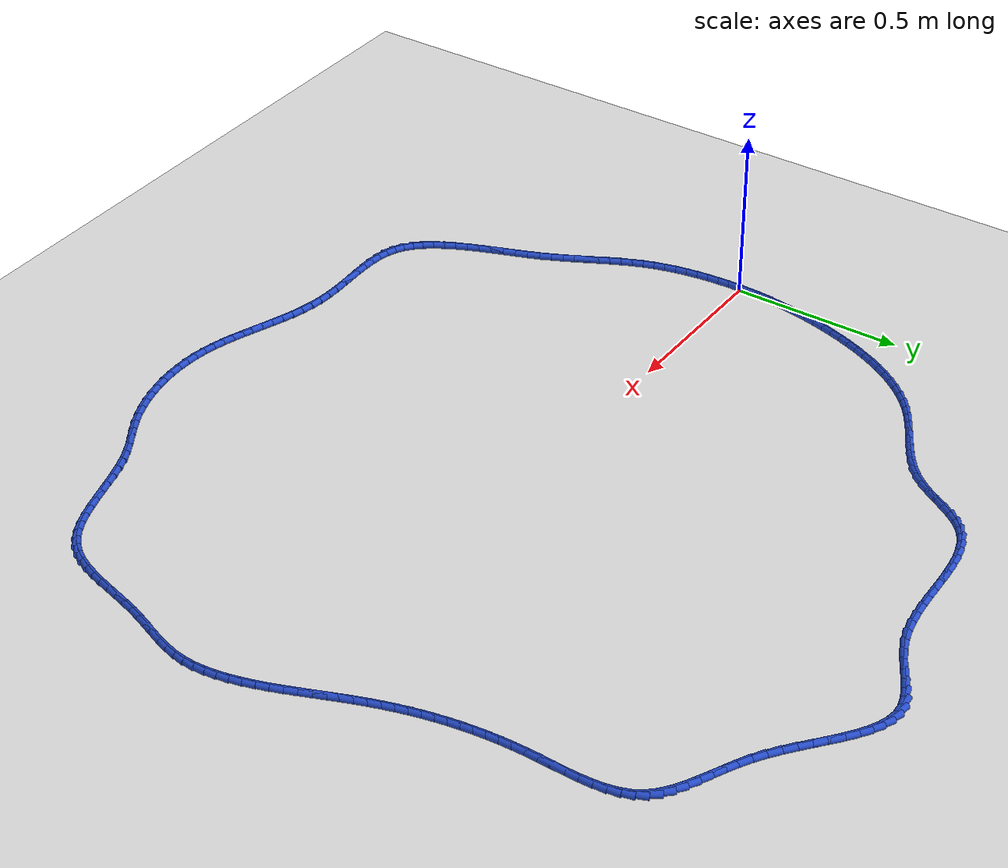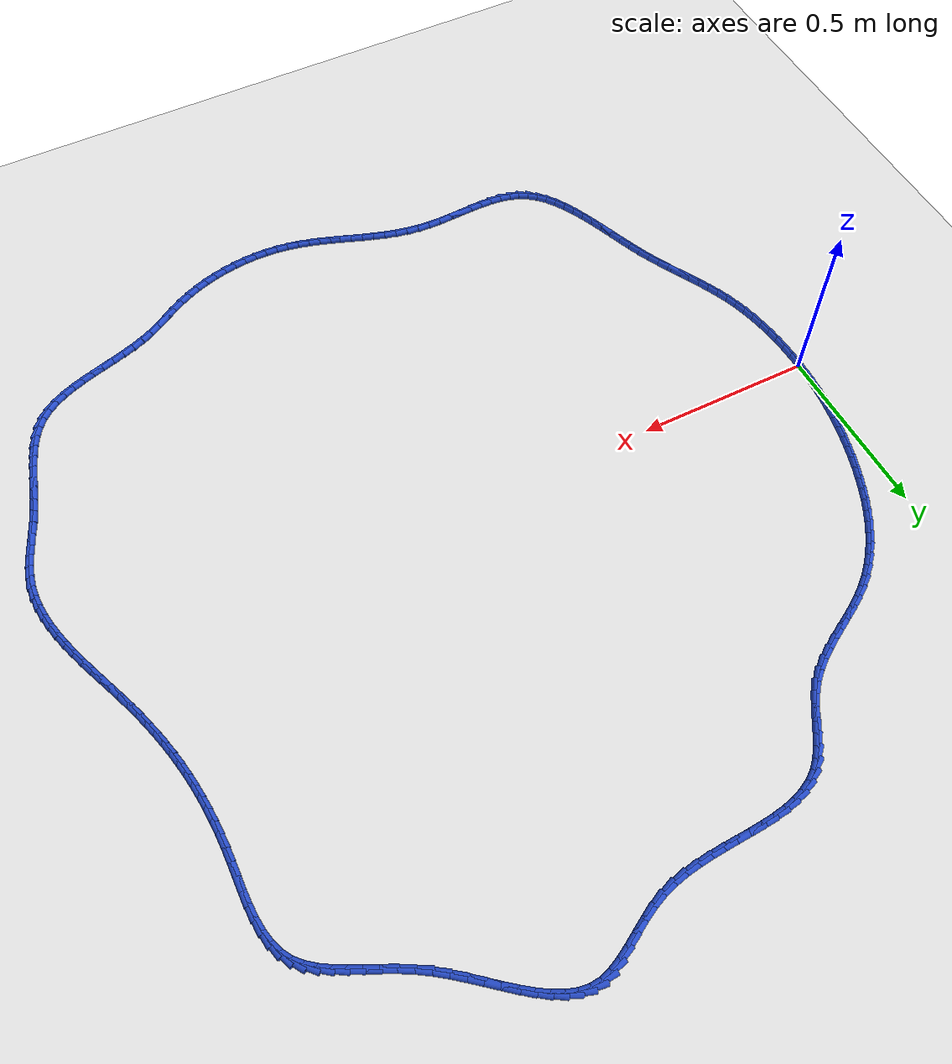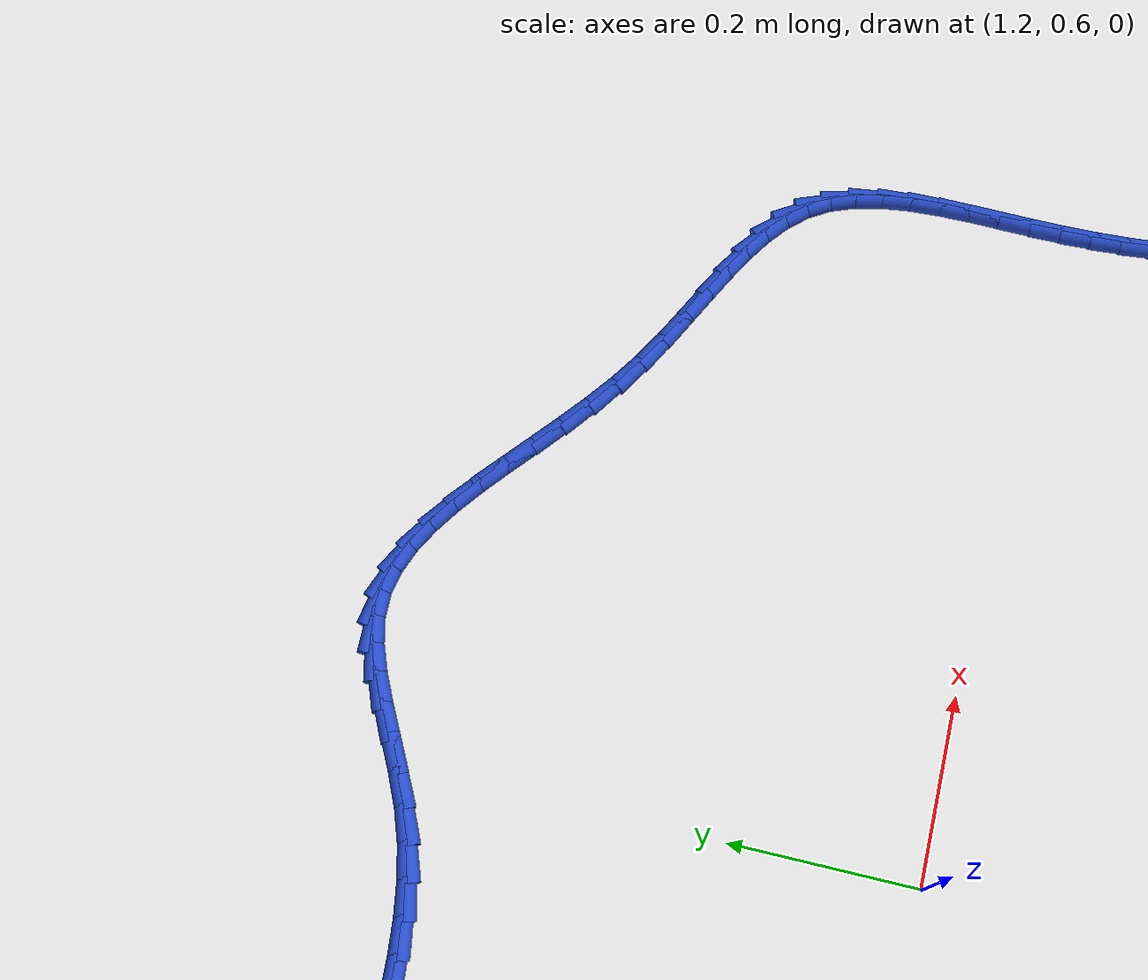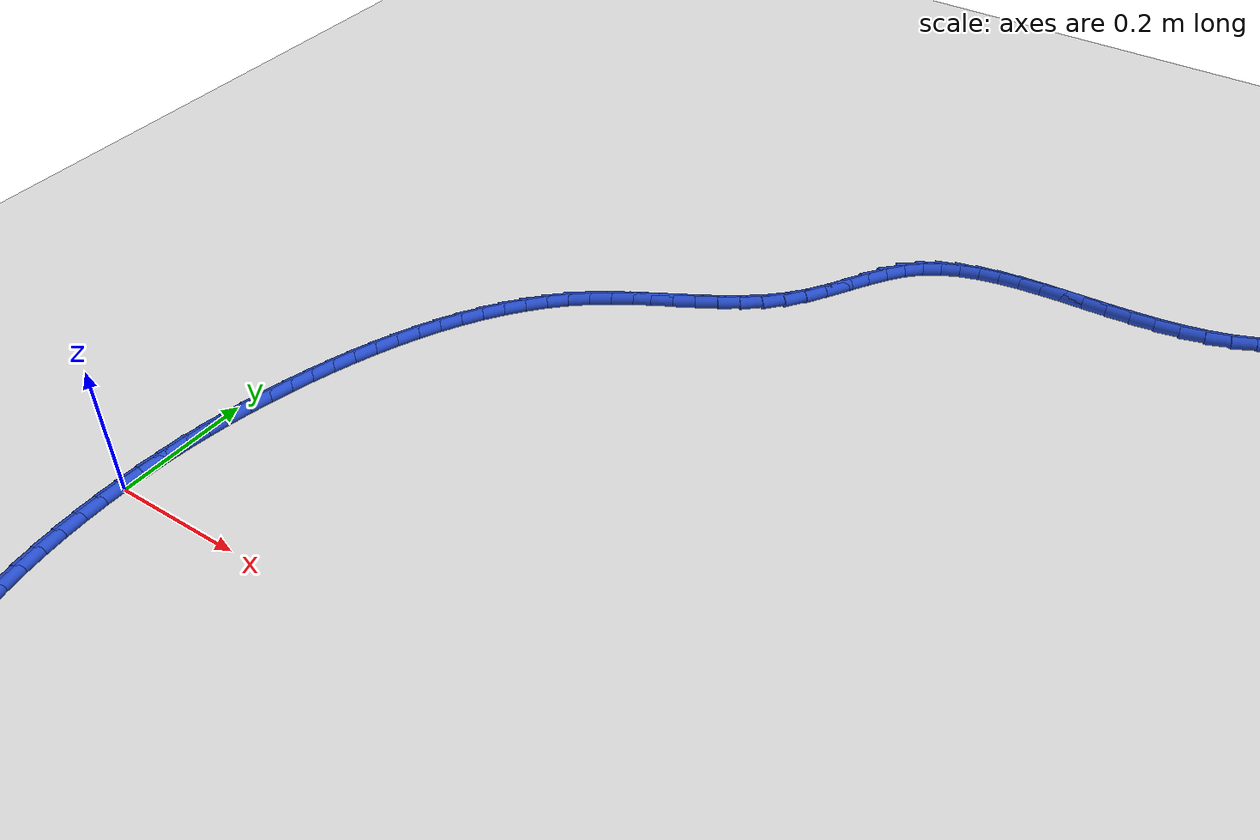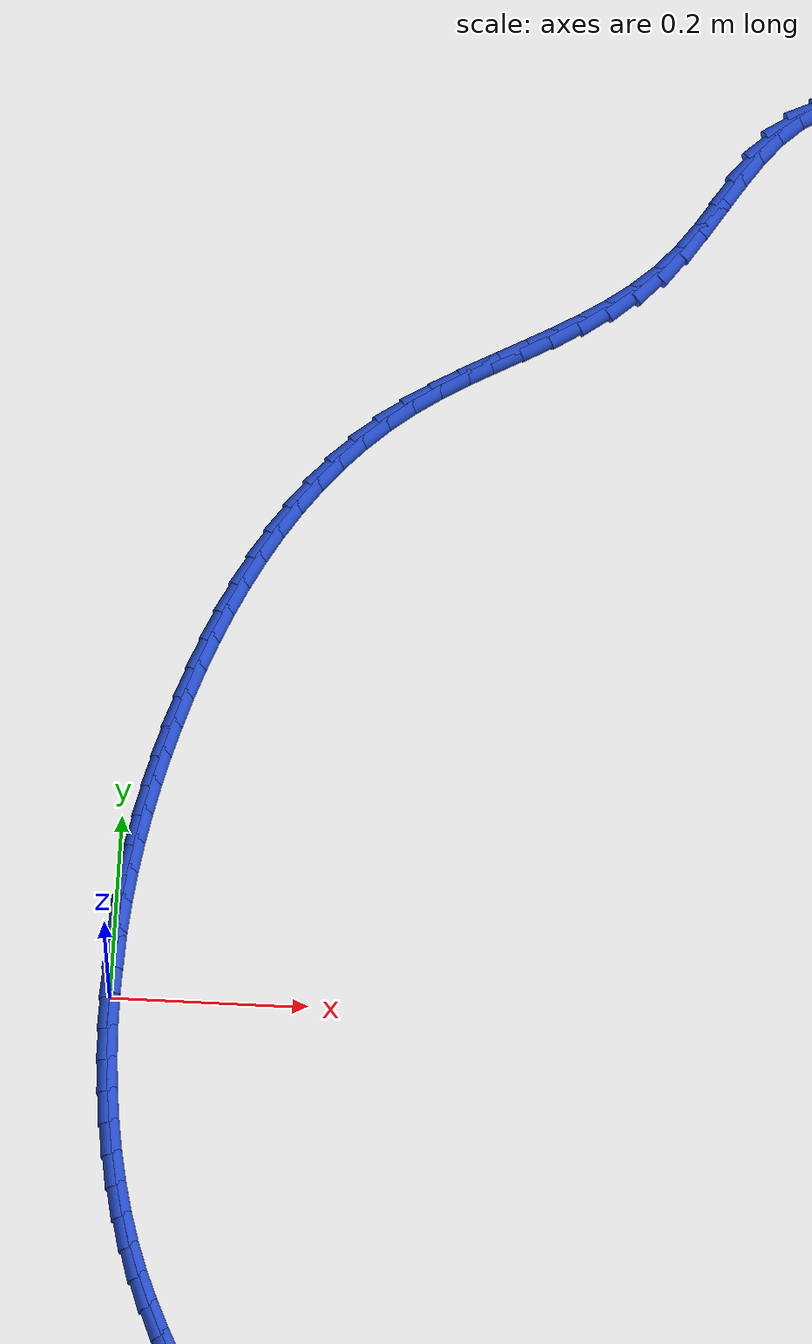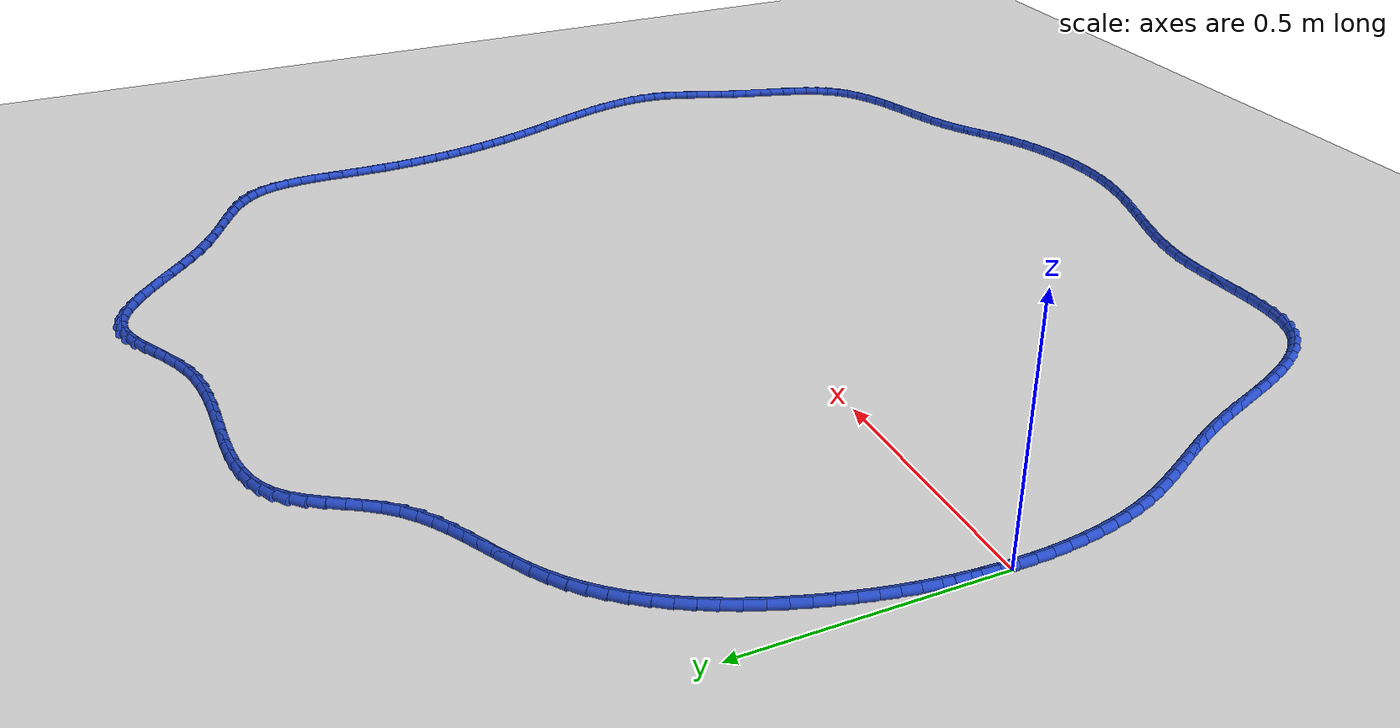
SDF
<sdf version="1.6">
 <world name="default">
  <light name="sun" type="directional">
   <pose>0 0 10 0 -0 0</pose>
   <diffuse>0.8 0.8 0.8 1</diffuse>
   <specular>0.2 0.2 0.2 1</specular>
   <attenuation>
    <range>1000</range>
    <constant>0.9</constant>
    <linear>0.01</linear>
    <quadratic>0.001</quadratic>
   </attenuation>
   <direction>-0.5 0.1 -0.9</direction>
  </light>
  <model name="ground_plane">
   <static>1</static>
   <link name="link">
    <collision name="collision">
     <geometry><plane><normal>0 0 1</normal><size>100 100</size></plane></geometry>
     <surface><friction><ode><mu>100</mu><mu2>50</mu2></ode></friction></surface>
    </collision>
    <visual name="visual">
     <cast_shadows>0</cast_shadows>
     <geometry><plane><normal>0 0 1</normal><size>100 100</size></plane></geometry>
     <material>
      <script><uri>file://media/materials/scripts/gazebo.material</uri><name>Gazebo/WhiteGlow</name></script>
     </material>
    </visual>
   </link>
  </model>
  <gravity>0 0 -9.8</gravity>
  <magnetic_field>6e-06 2.3e-05 -4.2e-05</magnetic_field>
  <atmosphere type="adiabatic"/>
  <physics name="default_physics" default="0" type="ode">
   <max_step_size>0.001</max_step_size>
   <real_time_factor>1</real_time_factor>
   <real_time_update_rate>1000</real_time_update_rate>
  </physics>
  <scene><ambient>0.4 0.4 0.4 1</ambient><background>0.7 0.7 0.7 1</background><shadows>1</shadows></scene>
  <spherical_coordinates>
   <surface_model>EARTH_WGS84</surface_model>
   <latitude_deg>0</latitude_deg>
   <longitude_deg>0</longitude_deg>
   <elevation>0</elevation>
   <heading_deg>0</heading_deg>
  </spherical_coordinates>
  <model name="line">
   <link name="link_0">
    <pose>1.9949319973733282e-17 1.0408340855860843e-16 0.01 0 1.57 1.5419335508537704</pose>
    <collision name="collision">
     <geometry><cylinder><radius>0.01</radius><length>0.08</length></cylinder></geometry>
    </collision>
    <visual name="visual">
     <material>
      <script><name>Gazebo/Blue</name><uri>file://media/materials/scripts/gazebo.material</uri></script>
     </material>
     <geometry><cylinder><radius>0.01</radius><length>0.08</length></cylinder></geometry>
    </visual>
   </link>
   <link name="link_1">
    <pose>0.0009726199615363683 0.033688716046483366 0.01 0 1.57 1.5105921317045155</pose>
    <collision name="collision">
     <geometry><cylinder><radius>0.01</radius><length>0.08</length></cylinder></geometry>
    </collision>
    <visual name="visual">
     <material>
      <script><name>Gazebo/Blue</name><uri>file://media/materials/scripts/gazebo.material</uri></script>
     </material>
     <geometry><cylinder><radius>0.01</radius><length>0.08</length></cylinder></geometry>
    </visual>
   </link>
   <link name="link_2">
    <pose>0.0029908607633866275 0.06717146268576321 0.01 0 1.57 1.4793949921731384</pose>
    <collision name="collision">
     <geometry><cylinder><radius>0.01</radius><length>0.08</length></cylinder></geometry>
    </collision>
    <visual name="visual">
     <material>
      <script><name>Gazebo/Blue</name><uri>file://media/materials/scripts/gazebo.material</uri></script>
     </material>
     <geometry><cylinder><radius>0.01</radius><length>0.08</length></cylinder></geometry>
    </visual>
   </link>
   <link name="link_3">
    <pose>0.006043759239022774 0.1004794251721321 0.01 0 1.57 1.4484889801887455</pose>
    <collision name="collision">
     <geometry><cylinder><radius>0.01</radius><length>0.08</length></cylinder></geometry>
    </collision>
    <visual name="visual">
     <material>
      <script><name>Gazebo/Blue</name><uri>file://media/materials/scripts/gazebo.material</uri></script>
     </material>
     <geometry><cylinder><radius>0.01</radius><length>0.08</length></cylinder></geometry>
    </visual>
   </link>
   <link name="link_4">
    <pose>0.010120352221916788 0.13364378875988256 0.01 0 1.57 1.4180166907970888</pose>
    <collision name="collision">
     <geometry><cylinder><radius>0.01</radius><length>0.08</length></cylinder></geometry>
    </collision>
    <visual name="visual">
     <material>
      <script><name>Gazebo/Blue</name><uri>file://media/materials/scripts/gazebo.material</uri></script>
     </material>
     <geometry><cylinder><radius>0.01</radius><length>0.08</length></cylinder></geometry>
    </visual>
   </link>
   <link name="link_5">
    <pose>0.015209676545540646 0.1666957387033071 0.01 0 1.57 1.3881135808997143</pose>
    <collision name="collision">
     <geometry><cylinder><radius>0.01</radius><length>0.08</length></cylinder></geometry>
    </collision>
    <visual name="visual">
     <material>
      <script><name>Gazebo/Blue</name><uri>file://media/materials/scripts/gazebo.material</uri></script>
     </material>
     <geometry><cylinder><radius>0.01</radius><length>0.08</length></cylinder></geometry>
    </visual>
   </link>
   <link name="link_6">
    <pose>0.02130076904336632 0.19966646025669818 0.01 0 1.57 1.3589054377201917</pose>
    <collision name="collision">
     <geometry><cylinder><radius>0.01</radius><length>0.08</length></cylinder></geometry>
    </collision>
    <visual name="visual">
     <material>
      <script><name>Gazebo/Blue</name><uri>file://media/materials/scripts/gazebo.material</uri></script>
     </material>
     <geometry><cylinder><radius>0.01</radius><length>0.08</length></cylinder></geometry>
    </visual>
   </link>
   <link name="link_7">
    <pose>0.028382666548865808 0.2325871386743484 0.01 0 1.57 1.3305063078921995</pose>
    <collision name="collision">
     <geometry><cylinder><radius>0.01</radius><length>0.08</length></cylinder></geometry>
    </collision>
    <visual name="visual">
     <material>
      <script><name>Gazebo/Blue</name><uri>file://media/materials/scripts/gazebo.material</uri></script>
     </material>
     <geometry><cylinder><radius>0.01</radius><length>0.08</length></cylinder></geometry>
    </visual>
   </link>
   <link name="link_8">
    <pose>0.03644440589551107 0.26548895921055027 0.01 0 1.57 1.3030162141385755</pose>
    <collision name="collision">
     <geometry><cylinder><radius>0.01</radius><length>0.08</length></cylinder></geometry>
    </collision>
    <visual name="visual">
     <material>
      <script><name>Gazebo/Blue</name><uri>file://media/materials/scripts/gazebo.material</uri></script>
     </material>
     <geometry><cylinder><radius>0.01</radius><length>0.08</length></cylinder></geometry>
    </visual>
   </link>
   <link name="link_9">
    <pose>0.045475038593171375 0.29840306513913895 0.01 0 1.57 1.2757563169907238</pose>
    <collision name="collision">
     <geometry><cylinder><radius>0.01</radius><length>0.08</length></cylinder></geometry>
    </collision>
    <visual name="visual">
     <material>
      <script><name>Gazebo/Blue</name><uri>file://media/materials/scripts/gazebo.material</uri></script>
     </material>
     <geometry><cylinder><radius>0.01</radius><length>0.08</length></cylinder></geometry>
    </visual>
   </link>
   <link name="link_10">
    <pose>0.05547835118894845 0.3313184515426218 0.01 0 1.57 1.2464646805544286</pose>
    <collision name="collision">
     <geometry><cylinder><radius>0.01</radius><length>0.08</length></cylinder></geometry>
    </collision>
    <visual name="visual">
     <material>
      <script><name>Gazebo/Blue</name><uri>file://media/materials/scripts/gazebo.material</uri></script>
     </material>
     <geometry><cylinder><radius>0.01</radius><length>0.08</length></cylinder></geometry>
    </visual>
   </link>
   <link name="link_11">
    <pose>0.06650055607922055 0.36410275834271794 0.01 0 1.57 1.2145175076593782</pose>
    <collision name="collision">
     <geometry><cylinder><radius>0.01</radius><length>0.08</length></cylinder></geometry>
    </collision>
    <visual name="visual">
     <material>
      <script><name>Gazebo/Blue</name><uri>file://media/materials/scripts/gazebo.material</uri></script>
     </material>
     <geometry><cylinder><radius>0.01</radius><length>0.08</length></cylinder></geometry>
    </visual>
   </link>
   <link name="link_12">
    <pose>0.0785954551267921 0.39660191650459864 0.01 0 1.57 1.1796495253171062</pose>
    <collision name="collision">
     <geometry><cylinder><radius>0.01</radius><length>0.08</length></cylinder></geometry>
    </collision>
    <visual name="visual">
     <material>
      <script><name>Gazebo/Blue</name><uri>file://media/materials/scripts/gazebo.material</uri></script>
     </material>
     <geometry><cylinder><radius>0.01</radius><length>0.08</length></cylinder></geometry>
    </visual>
   </link>
   <link name="link_13">
    <pose>0.09181685019446763 0.42866185699343556 0.01 0 1.57 1.1415731795454505</pose>
    <collision name="collision">
     <geometry><cylinder><radius>0.01</radius><length>0.08</length></cylinder></geometry>
    </collision>
    <visual name="visual">
     <material>
      <script><name>Gazebo/Blue</name><uri>file://media/materials/scripts/gazebo.material</uri></script>
     </material>
     <geometry><cylinder><radius>0.01</radius><length>0.08</length></cylinder></geometry>
    </visual>
   </link>
   <link name="link_14">
    <pose>0.10621854314505162 0.4601285107744 0.01 0 1.57 1.099983200029256</pose>
    <collision name="collision">
     <geometry><cylinder><radius>0.01</radius><length>0.08</length></cylinder></geometry>
    </collision>
    <visual name="visual">
     <material>
      <script><name>Gazebo/Blue</name><uri>file://media/materials/scripts/gazebo.material</uri></script>
     </material>
     <geometry><cylinder><radius>0.01</radius><length>0.08</length></cylinder></geometry>
    </visual>
   </link>
   <link name="link_15">
    <pose>0.12185433584134847 0.4908478088126632 0.01 0 1.57 1.0545647301251566</pose>
    <collision name="collision">
     <geometry><cylinder><radius>0.01</radius><length>0.08</length></cylinder></geometry>
    </collision>
    <visual name="visual">
     <material>
      <script><name>Gazebo/Blue</name><uri>file://media/materials/scripts/gazebo.material</uri></script>
     </material>
     <geometry><cylinder><radius>0.01</radius><length>0.08</length></cylinder></geometry>
    </visual>
   </link>
   <link name="link_16">
    <pose>0.13877803014616272 0.5206656820733967 0.01 0 1.57 1.0050064140622634</pose>
    <collision name="collision">
     <geometry><cylinder><radius>0.01</radius><length>0.08</length></cylinder></geometry>
    </collision>
    <visual name="visual">
     <material>
      <script><name>Gazebo/Blue</name><uri>file://media/materials/scripts/gazebo.material</uri></script>
     </material>
     <geometry><cylinder><radius>0.01</radius><length>0.08</length></cylinder></geometry>
    </visual>
   </link>
   <link name="link_17">
    <pose>0.15704342792229883 0.549428061521772 0.01 0 1.57 0.9510199638044261</pose>
    <collision name="collision">
     <geometry><cylinder><radius>0.01</radius><length>0.08</length></cylinder></geometry>
    </collision>
    <visual name="visual">
     <material>
      <script><name>Gazebo/Blue</name><uri>file://media/materials/scripts/gazebo.material</uri></script>
     </material>
     <geometry><cylinder><radius>0.01</radius><length>0.08</length></cylinder></geometry>
    </visual>
   </link>
   <link name="link_18">
    <pose>0.17670433103256128 0.5769808781229604 0.01 0 1.57 0.892367557888876</pose>
    <collision name="collision">
     <geometry><cylinder><radius>0.01</radius><length>0.08</length></cylinder></geometry>
    </collision>
    <visual name="visual">
     <material>
      <script><name>Gazebo/Blue</name><uri>file://media/materials/scripts/gazebo.material</uri></script>
     </material>
     <geometry><cylinder><radius>0.01</radius><length>0.08</length></cylinder></geometry>
    </visual>
   </link>
   <link name="link_19">
    <pose>0.19781454133975457 0.6031700628421331 0.01 0 1.57 0.8288976806914573</pose>
    <collision name="collision">
     <geometry><cylinder><radius>0.01</radius><length>0.08</length></cylinder></geometry>
    </collision>
    <visual name="visual">
     <material>
      <script><name>Gazebo/Blue</name><uri>file://media/materials/scripts/gazebo.material</uri></script>
     </material>
     <geometry><cylinder><radius>0.01</radius><length>0.08</length></cylinder></geometry>
    </visual>
   </link>
   <link name="link_20">
    <pose>0.2204278607066831 0.6278415466444618 0.01 0 1.57 0.7605883763736955</pose>
    <collision name="collision">
     <geometry><cylinder><radius>0.01</radius><length>0.08</length></cylinder></geometry>
    </collision>
    <visual name="visual">
     <material>
      <script><name>Gazebo/Blue</name><uri>file://media/materials/scripts/gazebo.material</uri></script>
     </material>
     <geometry><cylinder><radius>0.01</radius><length>0.08</length></cylinder></geometry>
    </visual>
   </link>
   <link name="link_21">
    <pose>0.24459809099615137 0.6508412604951177 0.01 0 1.57 0.6875941634903682</pose>
    <collision name="collision">
     <geometry><cylinder><radius>0.01</radius><length>0.08</length></cylinder></geometry>
    </collision>
    <visual name="visual">
     <material>
      <script><name>Gazebo/Blue</name><uri>file://media/materials/scripts/gazebo.material</uri></script>
     </material>
     <geometry><cylinder><radius>0.01</radius><length>0.08</length></cylinder></geometry>
    </visual>
   </link>
   <link name="link_22">
    <pose>0.270379034070964 0.6720151353592723 0.01 0 1.57 0.6140575735623199</pose>
    <collision name="collision">
     <geometry><cylinder><radius>0.01</radius><length>0.08</length></cylinder></geometry>
    </collision>
    <visual name="visual">
     <material>
      <script><name>Gazebo/Blue</name><uri>file://media/materials/scripts/gazebo.material</uri></script>
     </material>
     <geometry><cylinder><radius>0.01</radius><length>0.08</length></cylinder></geometry>
    </visual>
   </link>
   <link name="link_23">
    <pose>0.29774999726390533 0.6913109998456569 0.01 0 1.57 0.5572851478003247</pose>
    <collision name="collision">
     <geometry><cylinder><radius>0.01</radius><length>0.08</length></cylinder></geometry>
    </collision>
    <visual name="visual">
     <material>
      <script><name>Gazebo/Blue</name><uri>file://media/materials/scripts/gazebo.material</uri></script>
     </material>
     <geometry><cylinder><radius>0.01</radius><length>0.08</length></cylinder></geometry>
    </visual>
   </link>
   <link name="link_24">
    <pose>0.3263542034783766 0.7091363970062295 0.01 0 1.57 0.5217100630254482</pose>
    <collision name="collision">
     <geometry><cylinder><radius>0.01</radius><length>0.08</length></cylinder></geometry>
    </collision>
    <visual name="visual">
     <material>
      <script><name>Gazebo/Blue</name><uri>file://media/materials/scripts/gazebo.material</uri></script>
     </material>
     <geometry><cylinder><radius>0.01</radius><length>0.08</length></cylinder></geometry>
    </visual>
   </link>
   <link name="link_25">
    <pose>0.35574014031911266 0.7260284539535958 0.01 0 1.57 0.5067610405855049</pose>
    <collision name="collision">
     <geometry><cylinder><radius>0.01</radius><length>0.08</length></cylinder></geometry>
    </collision>
    <visual name="visual">
     <material>
      <script><name>Gazebo/Blue</name><uri>file://media/materials/scripts/gazebo.material</uri></script>
     </material>
     <geometry><cylinder><radius>0.01</radius><length>0.08</length></cylinder></geometry>
    </visual>
   </link>
   <link name="link_26">
    <pose>0.3854562899696529 0.7425243052157658 0.01 0 1.57 0.5121245256947354</pose>
    <collision name="collision">
     <geometry><cylinder><radius>0.01</radius><length>0.08</length></cylinder></geometry>
    </collision>
    <visual name="visual">
     <material>
      <script><name>Gazebo/Blue</name><uri>file://media/materials/scripts/gazebo.material</uri></script>
     </material>
     <geometry><cylinder><radius>0.01</radius><length>0.08</length></cylinder></geometry>
    </visual>
   </link>
   <link name="link_27">
    <pose>0.4150511346135368 0.7591610853207491 0.01 0 1.57 0.5379235069611435</pose>
    <collision name="collision">
     <geometry><cylinder><radius>0.01</radius><length>0.08</length></cylinder></geometry>
    </collision>
    <visual name="visual">
     <material>
      <script><name>Gazebo/Blue</name><uri>file://media/materials/scripts/gazebo.material</uri></script>
     </material>
     <geometry><cylinder><radius>0.01</radius><length>0.08</length></cylinder></geometry>
    </visual>
   </link>
   <link name="link_28">
    <pose>0.4440731564343042 0.7764759287965562 0.01 0 1.57 0.5846550095025621</pose>
    <collision name="collision">
     <geometry><cylinder><radius>0.01</radius><length>0.08</length></cylinder></geometry>
    </collision>
    <visual name="visual">
     <material>
      <script><name>Gazebo/Blue</name><uri>file://media/materials/scripts/gazebo.material</uri></script>
     </material>
     <geometry><cylinder><radius>0.01</radius><length>0.08</length></cylinder></geometry>
    </visual>
   </link>
   <link name="link_29">
    <pose>0.47207083761549384 0.7950059701711959 0.01 0 1.57 0.652869945618082</pose>
    <collision name="collision">
     <geometry><cylinder><radius>0.01</radius><length>0.08</length></cylinder></geometry>
    </collision>
    <visual name="visual">
     <material>
      <script><name>Gazebo/Blue</name><uri>file://media/materials/scripts/gazebo.material</uri></script>
     </material>
     <geometry><cylinder><radius>0.01</radius><length>0.08</length></cylinder></geometry>
    </visual>
   </link>
   <link name="link_30">
    <pose>0.49859266034064603 0.8152883439726789 0.01 0 1.57 0.7425419754409928</pose>
    <collision name="collision">
     <geometry><cylinder><radius>0.01</radius><length>0.08</length></cylinder></geometry>
    </collision>
    <visual name="visual">
     <material>
      <script><name>Gazebo/Blue</name><uri>file://media/materials/scripts/gazebo.material</uri></script>
     </material>
     <geometry><cylinder><radius>0.01</radius><length>0.08</length></cylinder></geometry>
    </visual>
   </link>
   <link name="link_31">
    <pose>0.5231871067932996 0.8378601847290144 0.01 0 1.57 0.8516283300620486</pose>
    <collision name="collision">
     <geometry><cylinder><radius>0.01</radius><length>0.08</length></cylinder></geometry>
    </collision>
    <visual name="visual">
     <material>
      <script><name>Gazebo/Blue</name><uri>file://media/materials/scripts/gazebo.material</uri></script>
     </material>
     <geometry><cylinder><radius>0.01</radius><length>0.08</length></cylinder></geometry>
    </visual>
   </link>
   <link name="link_32">
    <pose>0.545413233699303 0.8632441548730079 0.01 0 1.57 0.9515475418994285</pose>
    <collision name="collision">
     <geometry><cylinder><radius>0.01</radius><length>0.08</length></cylinder></geometry>
    </collision>
    <visual name="visual">
     <material>
      <script><name>Gazebo/Blue</name><uri>file://media/materials/scripts/gazebo.material</uri></script>
     </material>
     <geometry><cylinder><radius>0.01</radius><length>0.08</length></cylinder></geometry>
    </visual>
   </link>
   <link name="link_33">
    <pose>0.5653632146085769 0.8912333044146656 0.01 0 1.57 1.007120830123098</pose>
    <collision name="collision">
     <geometry><cylinder><radius>0.01</radius><length>0.08</length></cylinder></geometry>
    </collision>
    <visual name="visual">
     <material>
      <script><name>Gazebo/Blue</name><uri>file://media/materials/scripts/gazebo.material</uri></script>
     </material>
     <geometry><cylinder><radius>0.01</radius><length>0.08</length></cylinder></geometry>
    </visual>
   </link>
   <link name="link_34">
    <pose>0.5839020129180438 0.9205630595053527 0.01 0 1.57 1.018935335468079</pose>
    <collision name="collision">
     <geometry><cylinder><radius>0.01</radius><length>0.08</length></cylinder></geometry>
    </collision>
    <visual name="visual">
     <material>
      <script><name>Gazebo/Blue</name><uri>file://media/materials/scripts/gazebo.material</uri></script>
     </material>
     <geometry><cylinder><radius>0.01</radius><length>0.08</length></cylinder></geometry>
    </visual>
   </link>
   <link name="link_35">
    <pose>0.6019551820777126 0.9498859240298053 0.01 0 1.57 0.9865795366729746</pose>
    <collision name="collision">
     <geometry><cylinder><radius>0.01</radius><length>0.08</length></cylinder></geometry>
    </collision>
    <visual name="visual">
     <material>
      <script><name>Gazebo/Blue</name><uri>file://media/materials/scripts/gazebo.material</uri></script>
     </material>
     <geometry><cylinder><radius>0.01</radius><length>0.08</length></cylinder></geometry>
    </visual>
   </link>
   <link name="link_36">
    <pose>0.6204482755375922 0.97785440187276 0.01 0 1.57 0.9046742494875963</pose>
    <collision name="collision">
     <geometry><cylinder><radius>0.01</radius><length>0.08</length></cylinder></geometry>
    </collision>
    <visual name="visual">
     <material>
      <script><name>Gazebo/Blue</name><uri>file://media/materials/scripts/gazebo.material</uri></script>
     </material>
     <geometry><cylinder><radius>0.01</radius><length>0.08</length></cylinder></geometry>
    </visual>
   </link>
   <link name="link_37">
    <pose>0.6403068467476919 1.0031209969189532 0.01 0 1.57 0.7653309436785538</pose>
    <collision name="collision">
     <geometry><cylinder><radius>0.01</radius><length>0.08</length></cylinder></geometry>
    </collision>
    <visual name="visual">
     <material>
      <script><name>Gazebo/Blue</name><uri>file://media/materials/scripts/gazebo.material</uri></script>
     </material>
     <geometry><cylinder><radius>0.01</radius><length>0.08</length></cylinder></geometry>
    </visual>
   </link>
   <link name="link_38">
    <pose>0.6624327308869226 1.024376225858242 0.01 0 1.57 0.5978618893793848</pose>
    <collision name="collision">
     <geometry><cylinder><radius>0.01</radius><length>0.08</length></cylinder></geometry>
    </collision>
    <visual name="visual">
     <material>
      <script><name>Gazebo/Blue</name><uri>file://media/materials/scripts/gazebo.material</uri></script>
     </material>
     <geometry><cylinder><radius>0.01</radius><length>0.08</length></cylinder></geometry>
    </visual>
   </link>
   <link name="link_39">
    <pose>0.6871621846231105 1.0412170469012147 0.01 0 1.57 0.44583034565960933</pose>
    <collision name="collision">
     <geometry><cylinder><radius>0.01</radius><length>0.08</length></cylinder></geometry>
    </collision>
    <visual name="visual">
     <material>
      <script><name>Gazebo/Blue</name><uri>file://media/materials/scripts/gazebo.material</uri></script>
     </material>
     <geometry><cylinder><radius>0.01</radius><length>0.08</length></cylinder></geometry>
    </visual>
   </link>
   <link name="link_40">
    <pose>0.714254512961217 1.054165087305153 0.01 0 1.57 0.3183253424879754</pose>
    <collision name="collision">
     <geometry><cylinder><radius>0.01</radius><length>0.08</length></cylinder></geometry>
    </collision>
    <visual name="visual">
     <material>
      <script><name>Gazebo/Blue</name><uri>file://media/materials/scripts/gazebo.material</uri></script>
     </material>
     <geometry><cylinder><radius>0.01</radius><length>0.08</length></cylinder></geometry>
    </visual>
   </link>
   <link name="link_41">
    <pose>0.7434430277221029 1.0637836330906427 0.01 0 1.57 0.21742267575342825</pose>
    <collision name="collision">
     <geometry><cylinder><radius>0.01</radius><length>0.08</length></cylinder></geometry>
    </collision>
    <visual name="visual">
     <material>
      <script><name>Gazebo/Blue</name><uri>file://media/materials/scripts/gazebo.material</uri></script>
     </material>
     <geometry><cylinder><radius>0.01</radius><length>0.08</length></cylinder></geometry>
    </visual>
   </link>
   <link name="link_42">
    <pose>0.7744610407266291 1.0706359702782708 0.01 0 1.57 0.14174699650791195</pose>
    <collision name="collision">
     <geometry><cylinder><radius>0.01</radius><length>0.08</length></cylinder></geometry>
    </collision>
    <visual name="visual">
     <material>
      <script><name>Gazebo/Blue</name><uri>file://media/materials/scripts/gazebo.material</uri></script>
     </material>
     <geometry><cylinder><radius>0.01</radius><length>0.08</length></cylinder></geometry>
    </visual>
   </link>
   <link name="link_43">
    <pose>0.8070418637956578 1.0752853848886241 0.01 0 1.57 0.08861177686874201</pose>
    <collision name="collision">
     <geometry><cylinder><radius>0.01</radius><length>0.08</length></cylinder></geometry>
    </collision>
    <visual name="visual">
     <material>
      <script><name>Gazebo/Blue</name><uri>file://media/materials/scripts/gazebo.material</uri></script>
     </material>
     <geometry><cylinder><radius>0.01</radius><length>0.08</length></cylinder></geometry>
    </visual>
   </link>
   <link name="link_44">
    <pose>0.8409188087500497 1.0782951629422888 0.01 0 1.57 0.05533240665738422</pose>
    <collision name="collision">
     <geometry><cylinder><radius>0.01</radius><length>0.08</length></cylinder></geometry>
    </collision>
    <visual name="visual">
     <material>
      <script><name>Gazebo/Blue</name><uri>file://media/materials/scripts/gazebo.material</uri></script>
     </material>
     <geometry><cylinder><radius>0.01</radius><length>0.08</length></cylinder></geometry>
    </visual>
   </link>
   <link name="link_45">
    <pose>0.8758251874106653 1.0802285904598512 0.01 0 1.57 0.039799490561245134</pose>
    <collision name="collision">
     <geometry><cylinder><radius>0.01</radius><length>0.08</length></cylinder></geometry>
    </collision>
    <visual name="visual">
     <material>
      <script><name>Gazebo/Blue</name><uri>file://media/materials/scripts/gazebo.material</uri></script>
     </material>
     <geometry><cylinder><radius>0.01</radius><length>0.08</length></cylinder></geometry>
    </visual>
   </link>
   <link name="link_46">
    <pose>0.9114943115983671 1.0816489534618985 0.01 0 1.57 0.04064060295084018</pose>
    <collision name="collision">
     <geometry><cylinder><radius>0.01</radius><length>0.08</length></cylinder></geometry>
    </collision>
    <visual name="visual">
     <material>
      <script><name>Gazebo/Blue</name><uri>file://media/materials/scripts/gazebo.material</uri></script>
     </material>
     <geometry><cylinder><radius>0.01</radius><length>0.08</length></cylinder></geometry>
    </visual>
   </link>
   <link name="link_47">
    <pose>0.9476594931340157 1.0831195379690173 0.01 0 1.57 0.057201379007144906</pose>
    <collision name="collision">
     <geometry><cylinder><radius>0.01</radius><length>0.08</length></cylinder></geometry>
    </collision>
    <visual name="visual">
     <material>
      <script><name>Gazebo/Blue</name><uri>file://media/materials/scripts/gazebo.material</uri></script>
     </material>
     <geometry><cylinder><radius>0.01</radius><length>0.08</length></cylinder></geometry>
    </visual>
   </link>
   <link name="link_48">
    <pose>0.9840540438384727 1.085203630001794 0.01 0 1.57 0.08945080571969083</pose>
    <collision name="collision">
     <geometry><cylinder><radius>0.01</radius><length>0.08</length></cylinder></geometry>
    </collision>
    <visual name="visual">
     <material>
      <script><name>Gazebo/Blue</name><uri>file://media/materials/scripts/gazebo.material</uri></script>
     </material>
     <geometry><cylinder><radius>0.01</radius><length>0.08</length></cylinder></geometry>
    </visual>
   </link>
   <link name="link_49">
    <pose>1.0204112755325991 1.0884645155808148 0.01 0 1.57 0.13783112486434332</pose>
    <collision name="collision">
     <geometry><cylinder><radius>0.01</radius><length>0.08</length></cylinder></geometry>
    </collision>
    <visual name="visual">
     <material>
      <script><name>Gazebo/Blue</name><uri>file://media/materials/scripts/gazebo.material</uri></script>
     </material>
     <geometry><cylinder><radius>0.01</radius><length>0.08</length></cylinder></geometry>
    </visual>
   </link>
   <link name="link_50">
    <pose>1.0564645000372557 1.0934654807266666 0.01 0 1.57 0.20302099606714247</pose>
    <collision name="collision">
     <geometry><cylinder><radius>0.01</radius><length>0.08</length></cylinder></geometry>
    </collision>
    <visual name="visual">
     <material>
      <script><name>Gazebo/Blue</name><uri>file://media/materials/scripts/gazebo.material</uri></script>
     </material>
     <geometry><cylinder><radius>0.01</radius><length>0.08</length></cylinder></geometry>
    </visual>
   </link>
   <link name="link_51">
    <pose>1.0919470291733047 1.1007698114599362 0.01 0 1.57 0.2855528219127484</pose>
    <collision name="collision">
     <geometry><cylinder><radius>0.01</radius><length>0.08</length></cylinder></geometry>
    </collision>
    <visual name="visual">
     <material>
      <script><name>Gazebo/Blue</name><uri>file://media/materials/scripts/gazebo.material</uri></script>
     </material>
     <geometry><cylinder><radius>0.01</radius><length>0.08</length></cylinder></geometry>
    </visual>
   </link>
   <link name="link_52">
    <pose>1.1265921747616061 1.1109407938012097 0.01 0 1.57 0.38331383297517735</pose>
    <collision name="collision">
     <geometry><cylinder><radius>0.01</radius><length>0.08</length></cylinder></geometry>
    </collision>
    <visual name="visual">
     <material>
      <script><name>Gazebo/Blue</name><uri>file://media/materials/scripts/gazebo.material</uri></script>
     </material>
     <geometry><cylinder><radius>0.01</radius><length>0.08</length></cylinder></geometry>
    </visual>
   </link>
   <link name="link_53">
    <pose>1.160146334136835 1.1244718548027928 0.01 0 1.57 0.46564897024068913</pose>
    <collision name="collision">
     <geometry><cylinder><radius>0.01</radius><length>0.08</length></cylinder></geometry>
    </collision>
    <visual name="visual">
     <material>
      <script><name>Gazebo/Blue</name><uri>file://media/materials/scripts/gazebo.material</uri></script>
     </material>
     <geometry><cylinder><radius>0.01</radius><length>0.08</length></cylinder></geometry>
    </visual>
   </link>
   <link name="link_54">
    <pose>1.1925611931820037 1.1407604579657564 0.01 0 1.57 0.5103595775224526</pose>
    <collision name="collision">
     <geometry><cylinder><radius>0.01</radius><length>0.08</length></cylinder></geometry>
    </collision>
    <visual name="visual">
     <material>
      <script><name>Gazebo/Blue</name><uri>file://media/materials/scripts/gazebo.material</uri></script>
     </material>
     <geometry><cylinder><radius>0.01</radius><length>0.08</length></cylinder></geometry>
    </visual>
   </link>
   <link name="link_55">
    <pose>1.2239514683503903 1.158333703762203 0.01 0 1.57 0.5176873888681286</pose>
    <collision name="collision">
     <geometry><cylinder><radius>0.01</radius><length>0.08</length></cylinder></geometry>
    </collision>
    <visual name="visual">
     <material>
      <script><name>Gazebo/Blue</name><uri>file://media/materials/scripts/gazebo.material</uri></script>
     </material>
     <geometry><cylinder><radius>0.01</radius><length>0.08</length></cylinder></geometry>
    </visual>
   </link>
   <link name="link_56">
    <pose>1.2544363690275746 1.1756947064746546 0.01 0 1.57 0.4850304421787086</pose>
    <collision name="collision">
     <geometry><cylinder><radius>0.01</radius><length>0.08</length></cylinder></geometry>
    </collision>
    <visual name="visual">
     <material>
      <script><name>Gazebo/Blue</name><uri>file://media/materials/scripts/gazebo.material</uri></script>
     </material>
     <geometry><cylinder><radius>0.01</radius><length>0.08</length></cylinder></geometry>
    </visual>
   </link>
   <link name="link_57">
    <pose>1.2841351045991336 1.1913465803856331 0.01 0 1.57 0.4049985213432395</pose>
    <collision name="collision">
     <geometry><cylinder><radius>0.01</radius><length>0.08</length></cylinder></geometry>
    </collision>
    <visual name="visual">
     <material>
      <script><name>Gazebo/Blue</name><uri>file://media/materials/scripts/gazebo.material</uri></script>
     </material>
     <geometry><cylinder><radius>0.01</radius><length>0.08</length></cylinder></geometry>
    </visual>
   </link>
   <link name="link_58">
    <pose>1.313166884450647 1.2037924397776605 0.01 0 1.57 0.26542142345214836</pose>
    <collision name="collision">
     <geometry><cylinder><radius>0.01</radius><length>0.08</length></cylinder></geometry>
    </collision>
    <visual name="visual">
     <material>
      <script><name>Gazebo/Blue</name><uri>file://media/materials/scripts/gazebo.material</uri></script>
     </material>
     <geometry><cylinder><radius>0.01</radius><length>0.08</length></cylinder></geometry>
    </visual>
   </link>
   <link name="link_59">
    <pose>1.3416509179676923 1.211535398933259 0.01 0 1.57 0.06031166822615153</pose>
    <collision name="collision">
     <geometry><cylinder><radius>0.01</radius><length>0.08</length></cylinder></geometry>
    </collision>
    <visual name="visual">
     <material>
      <script><name>Gazebo/Blue</name><uri>file://media/materials/scripts/gazebo.material</uri></script>
     </material>
     <geometry><cylinder><radius>0.01</radius><length>0.08</length></cylinder></geometry>
    </visual>
   </link>
   <link name="link_60">
    <pose>1.3697072584119905 1.2132295783190832 0.01 0 1.57 -0.15415004500149007</pose>
    <collision name="collision">
     <geometry><cylinder><radius>0.01</radius><length>0.08</length></cylinder></geometry>
    </collision>
    <visual name="visual">
     <material>
      <script><name>Gazebo/Blue</name><uri>file://media/materials/scripts/gazebo.material</uri></script>
     </material>
     <geometry><cylinder><radius>0.01</radius><length>0.08</length></cylinder></geometry>
    </visual>
   </link>
   <link name="link_61">
    <pose>1.3974637134783245 1.2089167041035107 0.01 0 1.57 -0.33264679324486424</pose>
    <collision name="collision">
     <geometry><cylinder><radius>0.01</radius><length>0.08</length></cylinder></geometry>
    </collision>
    <visual name="visual">
     <material>
      <script><name>Gazebo/Blue</name><uri>file://media/materials/scripts/gazebo.material</uri></script>
     </material>
     <geometry><cylinder><radius>0.01</radius><length>0.08</length></cylinder></geometry>
    </visual>
   </link>
   <link name="link_62">
    <pose>1.4250522641023826 1.1993852769551159 0.01 0 1.57 -0.46880084862231314</pose>
    <collision name="collision">
     <geometry><cylinder><radius>0.01</radius><length>0.08</length></cylinder></geometry>
    </collision>
    <visual name="visual">
     <material>
      <script><name>Gazebo/Blue</name><uri>file://media/materials/scripts/gazebo.material</uri></script>
     </material>
     <geometry><cylinder><radius>0.01</radius><length>0.08</length></cylinder></geometry>
    </visual>
   </link>
   <link name="link_63">
    <pose>1.4526049314771863 1.1854310013323681 0.01 0 1.57 -0.5663874130373415</pose>
    <collision name="collision">
     <geometry><cylinder><radius>0.01</radius><length>0.08</length></cylinder></geometry>
    </collision>
    <visual name="visual">
     <material>
      <script><name>Gazebo/Blue</name><uri>file://media/materials/scripts/gazebo.material</uri></script>
     </material>
     <geometry><cylinder><radius>0.01</radius><length>0.08</length></cylinder></geometry>
    </visual>
   </link>
   <link name="link_64">
    <pose>1.4802537367957573 1.1678495816937384 0.01 0 1.57 -0.6320428697388675</pose>
    <collision name="collision">
     <geometry><cylinder><radius>0.01</radius><length>0.08</length></cylinder></geometry>
    </collision>
    <visual name="visual">
     <material>
      <script><name>Gazebo/Blue</name><uri>file://media/materials/scripts/gazebo.material</uri></script>
     </material>
     <geometry><cylinder><radius>0.01</radius><length>0.08</length></cylinder></geometry>
    </visual>
   </link>
   <link name="link_65">
    <pose>1.5081307012511185 1.147436722497697 0.01 0 1.57 -0.6716861099350321</pose>
    <collision name="collision">
     <geometry><cylinder><radius>0.01</radius><length>0.08</length></cylinder></geometry>
    </collision>
    <visual name="visual">
     <material>
      <script><name>Gazebo/Blue</name><uri>file://media/materials/scripts/gazebo.material</uri></script>
     </material>
     <geometry><cylinder><radius>0.01</radius><length>0.08</length></cylinder></geometry>
    </visual>
   </link>
   <link name="link_66">
    <pose>1.536367846036292 1.1249881282027132 0.01 0 1.57 -0.6895289632966681</pose>
    <collision name="collision">
     <geometry><cylinder><radius>0.01</radius><length>0.08</length></cylinder></geometry>
    </collision>
    <visual name="visual">
     <material>
      <script><name>Gazebo/Blue</name><uri>file://media/materials/scripts/gazebo.material</uri></script>
     </material>
     <geometry><cylinder><radius>0.01</radius><length>0.08</length></cylinder></geometry>
    </visual>
   </link>
   <link name="link_67">
    <pose>1.565097192344299 1.101299503267259 0.01 0 1.57 -0.6881001317095136</pose>
    <collision name="collision">
     <geometry><cylinder><radius>0.01</radius><length>0.08</length></cylinder></geometry>
    </collision>
    <visual name="visual">
     <material>
      <script><name>Gazebo/Blue</name><uri>file://media/materials/scripts/gazebo.material</uri></script>
     </material>
     <geometry><cylinder><radius>0.01</radius><length>0.08</length></cylinder></geometry>
    </visual>
   </link>
   <link name="link_68">
    <pose>1.5944507613681616 1.0771665521498035 0.01 0 1.57 -0.6685076442760897</pose>
    <collision name="collision">
     <geometry><cylinder><radius>0.01</radius><length>0.08</length></cylinder></geometry>
    </collision>
    <visual name="visual">
     <material>
      <script><name>Gazebo/Blue</name><uri>file://media/materials/scripts/gazebo.material</uri></script>
     </material>
     <geometry><cylinder><radius>0.01</radius><length>0.08</length></cylinder></geometry>
    </visual>
   </link>
   <link name="link_69">
    <pose>1.6245605743009028 1.053384979308817 0.01 0 1.57 -0.6307017678419294</pose>
    <collision name="collision">
     <geometry><cylinder><radius>0.01</radius><length>0.08</length></cylinder></geometry>
    </collision>
    <visual name="visual">
     <material>
      <script><name>Gazebo/Blue</name><uri>file://media/materials/scripts/gazebo.material</uri></script>
     </material>
     <geometry><cylinder><radius>0.01</radius><length>0.08</length></cylinder></geometry>
    </visual>
   </link>
   <link name="link_70">
    <pose>1.6555586523355434 1.0307504892027703 0.01 0 1.57 -0.5738004789861915</pose>
    <collision name="collision">
     <geometry><cylinder><radius>0.01</radius><length>0.08</length></cylinder></geometry>
    </collision>
    <visual name="visual">
     <material>
      <script><name>Gazebo/Blue</name><uri>file://media/materials/scripts/gazebo.material</uri></script>
     </material>
     <geometry><cylinder><radius>0.01</radius><length>0.08</length></cylinder></geometry>
    </visual>
   </link>
   <link name="link_71">
    <pose>1.6875757306218397 1.0100564574388695 0.01 0 1.57 -0.5095256205535255</pose>
    <collision name="collision">
     <geometry><cylinder><radius>0.01</radius><length>0.08</length></cylinder></geometry>
    </collision>
    <visual name="visual">
     <material>
      <script><name>Gazebo/Blue</name><uri>file://media/materials/scripts/gazebo.material</uri></script>
     </material>
     <geometry><cylinder><radius>0.01</radius><length>0.08</length></cylinder></geometry>
    </visual>
   </link>
   <link name="link_72">
    <pose>1.7205014499572242 0.9916596702016063 0.01 0 1.57 -0.46580849454297196</pose>
    <collision name="collision">
     <geometry><cylinder><radius>0.01</radius><length>0.08</length></cylinder></geometry>
    </collision>
    <visual name="visual">
     <material>
      <script><name>Gazebo/Blue</name><uri>file://media/materials/scripts/gazebo.material</uri></script>
     </material>
     <geometry><cylinder><radius>0.01</radius><length>0.08</length></cylinder></geometry>
    </visual>
   </link>
   <link name="link_73">
    <pose>1.7537022618001488 0.974969488199618 0.01 0 1.57 -0.44670020157682716</pose>
    <collision name="collision">
     <geometry><cylinder><radius>0.01</radius><length>0.08</length></cylinder></geometry>
    </collision>
    <visual name="visual">
     <material>
      <script><name>Gazebo/Blue</name><uri>file://media/materials/scripts/gazebo.material</uri></script>
     </material>
     <geometry><cylinder><radius>0.01</radius><length>0.08</length></cylinder></geometry>
    </visual>
   </link>
   <link name="link_74">
    <pose>1.7864760537995934 0.9592711123107235 0.01 0 1.57 -0.4534597389740223</pose>
    <collision name="collision">
     <geometry><cylinder><radius>0.01</radius><length>0.08</length></cylinder></geometry>
    </collision>
    <visual name="visual">
     <material>
      <script><name>Gazebo/Blue</name><uri>file://media/materials/scripts/gazebo.material</uri></script>
     </material>
     <geometry><cylinder><radius>0.01</radius><length>0.08</length></cylinder></geometry>
    </visual>
   </link>
   <link name="link_75">
    <pose>1.8181207136045388 0.9438497434127398 0.01 0 1.57 -0.48887749013990073</pose>
    <collision name="collision">
     <geometry><cylinder><radius>0.01</radius><length>0.08</length></cylinder></geometry>
    </collision>
    <visual name="visual">
     <material>
      <script><name>Gazebo/Blue</name><uri>file://media/materials/scripts/gazebo.material</uri></script>
     </material>
     <geometry><cylinder><radius>0.01</radius><length>0.08</length></cylinder></geometry>
    </visual>
   </link>
   <link name="link_76">
    <pose>1.8479341288639648 0.9279905823834836 0.01 0 1.57 -0.5575895091189957</pose>
    <collision name="collision">
     <geometry><cylinder><radius>0.01</radius><length>0.08</length></cylinder></geometry>
    </collision>
    <visual name="visual">
     <material>
      <script><name>Gazebo/Blue</name><uri>file://media/materials/scripts/gazebo.material</uri></script>
     </material>
     <geometry><cylinder><radius>0.01</radius><length>0.08</length></cylinder></geometry>
    </visual>
   </link>
   <link name="link_77">
    <pose>1.8752141872268528 0.9109788301007741 0.01 0 1.57 -0.6656339722998078</pose>
    <collision name="collision">
     <geometry><cylinder><radius>0.01</radius><length>0.08</length></cylinder></geometry>
    </collision>
    <visual name="visual">
     <material>
      <script><name>Gazebo/Blue</name><uri>file://media/materials/scripts/gazebo.material</uri></script>
     </material>
     <geometry><cylinder><radius>0.01</radius><length>0.08</length></cylinder></geometry>
    </visual>
   </link>
   <link name="link_78">
    <pose>1.8992587763421822 0.8920996874424277 0.01 0 1.57 -0.8179673193852823</pose>
    <collision name="collision">
     <geometry><cylinder><radius>0.01</radius><length>0.08</length></cylinder></geometry>
    </collision>
    <visual name="visual">
     <material>
      <script><name>Gazebo/Blue</name><uri>file://media/materials/scripts/gazebo.material</uri></script>
     </material>
     <geometry><cylinder><radius>0.01</radius><length>0.08</length></cylinder></geometry>
    </visual>
   </link>
   <link name="link_79">
    <pose>1.9193657838589333 0.8706383552862618 0.01 0 1.57 -1.010755072521734</pose>
    <collision name="collision">
     <geometry><cylinder><radius>0.01</radius><length>0.08</length></cylinder></geometry>
    </collision>
    <visual name="visual">
     <material>
      <script><name>Gazebo/Blue</name><uri>file://media/materials/scripts/gazebo.material</uri></script>
     </material>
     <geometry><cylinder><radius>0.01</radius><length>0.08</length></cylinder></geometry>
    </visual>
   </link>
   <link name="link_80">
    <pose>1.934869404800886 0.8459119634239772 0.01 0 1.57 -1.1985110948023179</pose>
    <collision name="collision">
     <geometry><cylinder><radius>0.01</radius><length>0.08</length></cylinder></geometry>
    </collision>
    <visual name="visual">
     <material>
      <script><name>Gazebo/Blue</name><uri>file://media/materials/scripts/gazebo.material</uri></script>
     </material>
     <geometry><cylinder><radius>0.01</radius><length>0.08</length></cylinder></geometry>
    </visual>
   </link>
   <link name="link_81">
    <pose>1.9458204738927953 0.8178678587154096 0.01 0 1.57 -1.3443204766195784</pose>
    <collision name="collision">
     <geometry><cylinder><radius>0.01</radius><length>0.08</length></cylinder></geometry>
    </collision>
    <visual name="visual">
     <material>
      <script><name>Gazebo/Blue</name><uri>file://media/materials/scripts/gazebo.material</uri></script>
     </material>
     <geometry><cylinder><radius>0.01</radius><length>0.08</length></cylinder></geometry>
    </visual>
   </link>
   <link name="link_82">
    <pose>1.9529262604362014 0.7870306603566029 0.01 0 1.57 -1.4507152748987588</pose>
    <collision name="collision">
     <geometry><cylinder><radius>0.01</radius><length>0.08</length></cylinder></geometry>
    </collision>
    <visual name="visual">
     <material>
      <script><name>Gazebo/Blue</name><uri>file://media/materials/scripts/gazebo.material</uri></script>
     </material>
     <geometry><cylinder><radius>0.01</radius><length>0.08</length></cylinder></geometry>
    </visual>
   </link>
   <link name="link_83">
    <pose>1.9569182710102144 0.7539463019446735 0.01 0 1.57 -1.5245532180694041</pose>
    <collision name="collision">
     <geometry><cylinder><radius>0.01</radius><length>0.08</length></cylinder></geometry>
    </collision>
    <visual name="visual">
     <material>
      <script><name>Gazebo/Blue</name><uri>file://media/materials/scripts/gazebo.material</uri></script>
     </material>
     <geometry><cylinder><radius>0.01</radius><length>0.08</length></cylinder></geometry>
    </visual>
   </link>
   <link name="link_84">
    <pose>1.9585280121939426 0.7191607170767358 0.01 0 1.57 1.5696549631936816</pose>
    <collision name="collision">
     <geometry><cylinder><radius>0.01</radius><length>0.08</length></cylinder></geometry>
    </collision>
    <visual name="visual">
     <material>
      <script><name>Gazebo/Blue</name><uri>file://media/materials/scripts/gazebo.material</uri></script>
     </material>
     <geometry><cylinder><radius>0.01</radius><length>0.08</length></cylinder></geometry>
    </visual>
   </link>
   <link name="link_85">
    <pose>1.9584869905664963 0.683219839349905 0.01 0 1.57 1.5445295476282128</pose>
    <collision name="collision">
     <geometry><cylinder><radius>0.01</radius><length>0.08</length></cylinder></geometry>
    </collision>
    <visual name="visual">
     <material>
      <script><name>Gazebo/Blue</name><uri>file://media/materials/scripts/gazebo.material</uri></script>
     </material>
     <geometry><cylinder><radius>0.01</radius><length>0.08</length></cylinder></geometry>
    </visual>
   </link>
   <link name="link_86">
    <pose>1.9575267127069853 0.6466696023612976 0.01 0 1.57 1.5394514291620447</pose>
    <collision name="collision">
     <geometry><cylinder><radius>0.01</radius><length>0.08</length></cylinder></geometry>
    </collision>
    <visual name="visual">
     <material>
      <script><name>Gazebo/Blue</name><uri>file://media/materials/scripts/gazebo.material</uri></script>
     </material>
     <geometry><cylinder><radius>0.01</radius><length>0.08</length></cylinder></geometry>
    </visual>
   </link>
   <link name="link_87">
    <pose>1.9563786851945175 0.6100559397080275 0.01 0 1.57 1.553838699194039</pose>
    <collision name="collision">
     <geometry><cylinder><radius>0.01</radius><length>0.08</length></cylinder></geometry>
    </collision>
    <visual name="visual">
     <material>
      <script><name>Gazebo/Blue</name><uri>file://media/materials/scripts/gazebo.material</uri></script>
     </material>
     <geometry><cylinder><radius>0.01</radius><length>0.08</length></cylinder></geometry>
    </visual>
   </link>
   <link name="link_88">
    <pose>1.9557658041441317 0.5739174941211393 0.01 0 1.57 -1.561365277810809</pose>
    <collision name="collision">
     <geometry><cylinder><radius>0.01</radius><length>0.08</length></cylinder></geometry>
    </collision>
    <visual name="visual">
     <material>
      <script><name>Gazebo/Blue</name><uri>file://media/materials/scripts/gazebo.material</uri></script>
     </material>
     <geometry><cylinder><radius>0.01</radius><length>0.08</length></cylinder></geometry>
    </visual>
   </link>
   <link name="link_89">
    <pose>1.9560995624985185 0.5385292293006194 0.01 0 1.57 -1.5333334870522062</pose>
    <collision name="collision">
     <geometry><cylinder><radius>0.01</radius><length>0.08</length></cylinder></geometry>
    </collision>
    <visual name="visual">
     <material>
      <script><name>Gazebo/Blue</name><uri>file://media/materials/scripts/gazebo.material</uri></script>
     </material>
     <geometry><cylinder><radius>0.01</radius><length>0.08</length></cylinder></geometry>
    </visual>
   </link>
   <link name="link_90">
    <pose>1.9573999306363246 0.5038345892334474 0.01 0 1.57 -1.5045162207937364</pose>
    <collision name="collision">
     <geometry><cylinder><radius>0.01</radius><length>0.08</length></cylinder></geometry>
    </collision>
    <visual name="visual">
     <material>
      <script><name>Gazebo/Blue</name><uri>file://media/materials/scripts/gazebo.material</uri></script>
     </material>
     <geometry><cylinder><radius>0.01</radius><length>0.08</length></cylinder></geometry>
    </visual>
   </link>
   <link name="link_91">
    <pose>1.9596619808200568 0.4697559355550987 0.01 0 1.57 -1.4751210772694785</pose>
    <collision name="collision">
     <geometry><cylinder><radius>0.01</radius><length>0.08</length></cylinder></geometry>
    </collision>
    <visual name="visual">
     <material>
      <script><name>Gazebo/Blue</name><uri>file://media/materials/scripts/gazebo.material</uri></script>
     </material>
     <geometry><cylinder><radius>0.01</radius><length>0.08</length></cylinder></geometry>
    </visual>
   </link>
   <link name="link_92">
    <pose>1.962880785312221 0.43621562990104806 0.01 0 1.57 -1.4453794105737736</pose>
    <collision name="collision">
     <geometry><cylinder><radius>0.01</radius><length>0.08</length></cylinder></geometry>
    </collision>
    <visual name="visual">
     <material>
      <script><name>Gazebo/Blue</name><uri>file://media/materials/scripts/gazebo.material</uri></script>
     </material>
     <geometry><cylinder><radius>0.01</radius><length>0.08</length></cylinder></geometry>
    </visual>
   </link>
   <link name="link_93">
    <pose>1.9670514163753237 0.40313603390677144 0.01 0 1.57 -1.4155399157731614</pose>
    <collision name="collision">
     <geometry><cylinder><radius>0.01</radius><length>0.08</length></cylinder></geometry>
    </collision>
    <visual name="visual">
     <material>
      <script><name>Gazebo/Blue</name><uri>file://media/materials/scripts/gazebo.material</uri></script>
     </material>
     <geometry><cylinder><radius>0.01</radius><length>0.08</length></cylinder></geometry>
    </visual>
   </link>
   <link name="link_94">
    <pose>1.97216894627187 0.3704395092077433 0.01 0 1.57 -1.385860838722478</pose>
    <collision name="collision">
     <geometry><cylinder><radius>0.01</radius><length>0.08</length></cylinder></geometry>
    </collision>
    <visual name="visual">
     <material>
      <script><name>Gazebo/Blue</name><uri>file://media/materials/scripts/gazebo.material</uri></script>
     </material>
     <geometry><cylinder><radius>0.01</radius><length>0.08</length></cylinder></geometry>
    </visual>
   </link>
   <link name="link_95">
    <pose>1.9782284472643663 0.3380484174394385 0.01 0 1.57 -1.3566013604336506</pose>
    <collision name="collision">
     <geometry><cylinder><radius>0.01</radius><length>0.08</length></cylinder></geometry>
    </collision>
    <visual name="visual">
     <material>
      <script><name>Gazebo/Blue</name><uri>file://media/materials/scripts/gazebo.material</uri></script>
     </material>
     <geometry><cylinder><radius>0.01</radius><length>0.08</length></cylinder></geometry>
    </visual>
   </link>
   <link name="link_96">
    <pose>1.985224991615319 0.305885120237333 0.01 0 1.57 -1.328012824327587</pose>
    <collision name="collision">
     <geometry><cylinder><radius>0.01</radius><length>0.08</length></cylinder></geometry>
    </collision>
    <visual name="visual">
     <material>
      <script><name>Gazebo/Blue</name><uri>file://media/materials/scripts/gazebo.material</uri></script>
     </material>
     <geometry><cylinder><radius>0.01</radius><length>0.08</length></cylinder></geometry>
    </visual>
   </link>
   <link name="link_97">
    <pose>1.9931536515872343 0.27387197923690126 0.01 0 1.57 -1.3003304993357787</pose>
    <collision name="collision">
     <geometry><cylinder><radius>0.01</radius><length>0.08</length></cylinder></geometry>
    </collision>
    <visual name="visual">
     <material>
      <script><name>Gazebo/Blue</name><uri>file://media/materials/scripts/gazebo.material</uri></script>
     </material>
     <geometry><cylinder><radius>0.01</radius><length>0.08</length></cylinder></geometry>
    </visual>
   </link>
   <link name="link_98">
    <pose>2.0020094994426176 0.24193135607361818 0.01 0 1.57 -1.2737664969563371</pose>
    <collision name="collision">
     <geometry><cylinder><radius>0.01</radius><length>0.08</length></cylinder></geometry>
    </collision>
    <visual name="visual">
     <material>
      <script><name>Gazebo/Blue</name><uri>file://media/materials/scripts/gazebo.material</uri></script>
     </material>
     <geometry><cylinder><radius>0.01</radius><length>0.08</length></cylinder></geometry>
    </visual>
   </link>
   <link name="link_99">
    <pose>2.0117876074439756 0.20998561238295965 0.01 0 1.57 -1.2485043027606284</pose>
    <collision name="collision">
     <geometry><cylinder><radius>0.01</radius><length>0.08</length></cylinder></geometry>
    </collision>
    <visual name="visual">
     <material>
      <script><name>Gazebo/Blue</name><uri>file://media/materials/scripts/gazebo.material</uri></script>
     </material>
     <geometry><cylinder><radius>0.01</radius><length>0.08</length></cylinder></geometry>
    </visual>
   </link>
   <link name="link_100">
    <pose>2.0224830478538136 0.1779571098004003 0.01 0 1.57 -1.2246988902339082</pose>
    <collision name="collision">
     <geometry><cylinder><radius>0.01</radius><length>0.08</length></cylinder></geometry>
    </collision>
    <visual name="visual">
     <material>
      <script><name>Gazebo/Blue</name><uri>file://media/materials/scripts/gazebo.material</uri></script>
     </material>
     <geometry><cylinder><radius>0.01</radius><length>0.08</length></cylinder></geometry>
    </visual>
   </link>
   <link name="link_101">
    <pose>2.0340907359773226 0.14576827058842837 0.01 0 1.57 -1.204222264813193</pose>
    <collision name="collision">
     <geometry><cylinder><radius>0.01</radius><length>0.08</length></cylinder></geometry>
    </collision>
    <visual name="visual">
     <material>
      <script><name>Gazebo/Blue</name><uri>file://media/materials/scripts/gazebo.material</uri></script>
     </material>
     <geometry><cylinder><radius>0.01</radius><length>0.08</length></cylinder></geometry>
    </visual>
   </link>
   <link name="link_102">
    <pose>2.0465288662500067 0.1133711515453364 0.01 0 1.57 -1.191448512287862</pose>
    <collision name="collision">
     <geometry><cylinder><radius>0.01</radius><length>0.08</length></cylinder></geometry>
    </collision>
    <visual name="visual">
     <material>
      <script><name>Gazebo/Blue</name><uri>file://media/materials/scripts/gazebo.material</uri></script>
     </material>
     <geometry><cylinder><radius>0.01</radius><length>0.08</length></cylinder></geometry>
    </visual>
   </link>
   <link name="link_103">
    <pose>2.0595155255640383 0.08079510387681492 0.01 0 1.57 -1.1867167551376274</pose>
    <collision name="collision">
     <geometry><cylinder><radius>0.01</radius><length>0.08</length></cylinder></geometry>
    </collision>
    <visual name="visual">
     <material>
      <script><name>Gazebo/Blue</name><uri>file://media/materials/scripts/gazebo.material</uri></script>
     </material>
     <geometry><cylinder><radius>0.01</radius><length>0.08</length></cylinder></geometry>
    </visual>
   </link>
   <link name="link_104">
    <pose>2.0727365859225877 0.04808192225127021 0.01 0 1.57 -1.1898190442919476</pose>
    <collision name="collision">
     <geometry><cylinder><radius>0.01</radius><length>0.08</length></cylinder></geometry>
    </collision>
    <visual name="visual">
     <material>
      <script><name>Gazebo/Blue</name><uri>file://media/materials/scripts/gazebo.material</uri></script>
     </material>
     <geometry><cylinder><radius>0.01</radius><length>0.08</length></cylinder></geometry>
    </visual>
   </link>
   <link name="link_105">
    <pose>2.085877919328829 0.01527340133710866 0.01 0 1.57 -1.200756814366839</pose>
    <collision name="collision">
     <geometry><cylinder><radius>0.01</radius><length>0.08</length></cylinder></geometry>
    </collision>
    <visual name="visual">
     <material>
      <script><name>Gazebo/Blue</name><uri>file://media/materials/scripts/gazebo.material</uri></script>
     </material>
     <geometry><cylinder><radius>0.01</radius><length>0.08</length></cylinder></geometry>
    </visual>
   </link>
   <link name="link_106">
    <pose>2.0986253977859346 -0.017588664197264056 0.01 0 1.57 -1.219733337115409</pose>
    <collision name="collision">
     <geometry><cylinder><radius>0.01</radius><length>0.08</length></cylinder></geometry>
    </collision>
    <visual name="visual">
     <material>
      <script><name>Gazebo/Blue</name><uri>file://media/materials/scripts/gazebo.material</uri></script>
     </material>
     <geometry><cylinder><radius>0.01</radius><length>0.08</length></cylinder></geometry>
    </visual>
   </link>
   <link name="link_107">
    <pose>2.110664893297076 -0.050462479683440184 0.01 0 1.57 -1.2471435801305075</pose>
    <collision name="collision">
     <geometry><cylinder><radius>0.01</radius><length>0.08</length></cylinder></geometry>
    </collision>
    <visual name="visual">
     <material>
      <script><name>Gazebo/Blue</name><uri>file://media/materials/scripts/gazebo.material</uri></script>
     </material>
     <geometry><cylinder><radius>0.01</radius><length>0.08</length></cylinder></geometry>
    </visual>
   </link>
   <link name="link_108">
    <pose>2.1216822778654256 -0.08330625045301401 0.01 0 1.57 -1.2835561411072995</pose>
    <collision name="collision">
     <geometry><cylinder><radius>0.01</radius><length>0.08</length></cylinder></geometry>
    </collision>
    <visual name="visual">
     <material>
      <script><name>Gazebo/Blue</name><uri>file://media/materials/scripts/gazebo.material</uri></script>
     </material>
     <geometry><cylinder><radius>0.01</radius><length>0.08</length></cylinder></geometry>
    </visual>
   </link>
   <link name="link_109">
    <pose>2.131363423494156 -0.11607818183757922 0.01 0 1.57 -1.3296772092463849</pose>
    <collision name="collision">
     <geometry><cylinder><radius>0.01</radius><length>0.08</length></cylinder></geometry>
    </collision>
    <visual name="visual">
     <material>
      <script><name>Gazebo/Blue</name><uri>file://media/materials/scripts/gazebo.material</uri></script>
     </material>
     <geometry><cylinder><radius>0.01</radius><length>0.08</length></cylinder></geometry>
    </visual>
   </link>
   <link name="link_110">
    <pose>2.13939420218644 -0.14873647916872945 0.01 0 1.57 -1.3862808337458743</pose>
    <collision name="collision">
     <geometry><cylinder><radius>0.01</radius><length>0.08</length></cylinder></geometry>
    </collision>
    <visual name="visual">
     <material>
      <script><name>Gazebo/Blue</name><uri>file://media/materials/scripts/gazebo.material</uri></script>
     </material>
     <geometry><cylinder><radius>0.01</radius><length>0.08</length></cylinder></geometry>
    </visual>
   </link>
   <link name="link_111">
    <pose>2.145460485945449 -0.18123934777805834 0.01 0 1.57 -1.454084614795943</pose>
    <collision name="collision">
     <geometry><cylinder><radius>0.01</radius><length>0.08</length></cylinder></geometry>
    </collision>
    <visual name="visual">
     <material>
      <script><name>Gazebo/Blue</name><uri>file://media/materials/scripts/gazebo.material</uri></script>
     </material>
     <geometry><cylinder><radius>0.01</radius><length>0.08</length></cylinder></geometry>
    </visual>
   </link>
   <link name="link_112">
    <pose>2.1492481467743567 -0.21354499299716023 0.01 0 1.57 -1.5335502114042325</pose>
    <collision name="collision">
     <geometry><cylinder><radius>0.01</radius><length>0.08</length></cylinder></geometry>
    </collision>
    <visual name="visual">
     <material>
      <script><name>Gazebo/Blue</name><uri>file://media/materials/scripts/gazebo.material</uri></script>
     </material>
     <geometry><cylinder><radius>0.01</radius><length>0.08</length></cylinder></geometry>
    </visual>
   </link>
   <link name="link_113">
    <pose>2.150443056676334 -0.24561162015762728 0.01 0 1.57 1.5169887859256022</pose>
    <collision name="collision">
     <geometry><cylinder><radius>0.01</radius><length>0.08</length></cylinder></geometry>
    </collision>
    <visual name="visual">
     <material>
      <script><name>Gazebo/Blue</name><uri>file://media/materials/scripts/gazebo.material</uri></script>
     </material>
     <geometry><cylinder><radius>0.01</radius><length>0.08</length></cylinder></geometry>
    </visual>
   </link>
   <link name="link_114">
    <pose>2.1487310876545545 -0.2773974345910539 0.01 0 1.57 1.415580327125794</pose>
    <collision name="collision">
     <geometry><cylinder><radius>0.01</radius><length>0.08</length></cylinder></geometry>
    </collision>
    <visual name="visual">
     <material>
      <script><name>Gazebo/Blue</name><uri>file://media/materials/scripts/gazebo.material</uri></script>
     </material>
     <geometry><cylinder><radius>0.01</radius><length>0.08</length></cylinder></geometry>
    </visual>
   </link>
   <link name="link_115">
    <pose>2.1438075494712425 -0.308862845615186 0.01 0 1.57 1.3197248190101092</pose>
    <collision name="collision">
     <geometry><cylinder><radius>0.01</radius><length>0.08</length></cylinder></geometry>
    </collision>
    <visual name="visual">
     <material>
      <script><name>Gazebo/Blue</name><uri>file://media/materials/scripts/gazebo.material</uri></script>
     </material>
     <geometry><cylinder><radius>0.01</radius><length>0.08</length></cylinder></geometry>
    </visual>
   </link>
   <link name="link_116">
    <pose>2.1358034248707756 -0.34007000462597475 0.01 0 1.57 1.250202705621795</pose>
    <collision name="collision">
     <geometry><cylinder><radius>0.01</radius><length>0.08</length></cylinder></geometry>
    </collision>
    <visual name="visual">
     <material>
      <script><name>Gazebo/Blue</name><uri>file://media/materials/scripts/gazebo.material</uri></script>
     </material>
     <geometry><cylinder><radius>0.01</radius><length>0.08</length></cylinder></geometry>
    </visual>
   </link>
   <link name="link_117">
    <pose>2.1254590066093755 -0.3712233543007118 0.01 0 1.57 1.207663755966458</pose>
    <collision name="collision">
     <geometry><cylinder><radius>0.01</radius><length>0.08</length></cylinder></geometry>
    </collision>
    <visual name="visual">
     <material>
      <script><name>Gazebo/Blue</name><uri>file://media/materials/scripts/gazebo.material</uri></script>
     </material>
     <geometry><cylinder><radius>0.01</radius><length>0.08</length></cylinder></geometry>
    </visual>
   </link>
   <link name="link_118">
    <pose>2.113559982142518 -0.40253793827481776 0.01 0 1.57 1.190518513195598</pose>
    <collision name="collision">
     <geometry><cylinder><radius>0.01</radius><length>0.08</length></cylinder></geometry>
    </collision>
    <visual name="visual">
     <material>
      <script><name>Gazebo/Blue</name><uri>file://media/materials/scripts/gazebo.material</uri></script>
     </material>
     <geometry><cylinder><radius>0.01</radius><length>0.08</length></cylinder></geometry>
    </visual>
   </link>
   <link name="link_119">
    <pose>2.1008920389256778 -0.4342288001837139 0.01 0 1.57 1.1972978768963247</pose>
    <collision name="collision">
     <geometry><cylinder><radius>0.01</radius><length>0.08</length></cylinder></geometry>
    </collision>
    <visual name="visual">
     <material>
      <script><name>Gazebo/Blue</name><uri>file://media/materials/scripts/gazebo.material</uri></script>
     </material>
     <geometry><cylinder><radius>0.01</radius><length>0.08</length></cylinder></geometry>
    </visual>
   </link>
   <link name="link_120">
    <pose>2.088240864414333 -0.46651098366281973 0.01 0 1.57 1.2268689305005518</pose>
    <collision name="collision">
     <geometry><cylinder><radius>0.01</radius><length>0.08</length></cylinder></geometry>
    </collision>
    <visual name="visual">
     <material>
      <script><name>Gazebo/Blue</name><uri>file://media/materials/scripts/gazebo.material</uri></script>
     </material>
     <geometry><cylinder><radius>0.01</radius><length>0.08</length></cylinder></geometry>
    </visual>
   </link>
   <link name="link_121">
    <pose>2.0763901775436104 -0.49959849959278524 0.01 0 1.57 1.2665996241157482</pose>
    <collision name="collision">
     <geometry><cylinder><radius>0.01</radius><length>0.08</length></cylinder></geometry>
    </collision>
    <visual name="visual">
     <material>
      <script><name>Gazebo/Blue</name><uri>file://media/materials/scripts/gazebo.material</uri></script>
     </material>
     <geometry><cylinder><radius>0.01</radius><length>0.08</length></cylinder></geometry>
    </visual>
   </link>
   <link name="link_122">
    <pose>2.065745021419627 -0.5335066922419005 0.01 0 1.57 1.290928732849277</pose>
    <collision name="collision">
     <geometry><cylinder><radius>0.01</radius><length>0.08</length></cylinder></geometry>
    </collision>
    <visual name="visual">
     <material>
      <script><name>Gazebo/Blue</name><uri>file://media/materials/scripts/gazebo.material</uri></script>
     </material>
     <geometry><cylinder><radius>0.01</radius><length>0.08</length></cylinder></geometry>
    </visual>
   </link>
   <link name="link_123">
    <pose>2.055883798735134 -0.5678172213441313 0.01 0 1.57 1.2972048636019677</pose>
    <collision name="collision">
     <geometry><cylinder><radius>0.01</radius><length>0.08</length></cylinder></geometry>
    </collision>
    <visual name="visual">
     <material>
      <script><name>Gazebo/Blue</name><uri>file://media/materials/scripts/gazebo.material</uri></script>
     </material>
     <geometry><cylinder><radius>0.01</radius><length>0.08</length></cylinder></geometry>
    </visual>
   </link>
   <link name="link_124">
    <pose>2.0462758349655066 -0.6020545209020888 0.01 0 1.57 1.2853734830545551</pose>
    <collision name="collision">
     <geometry><cylinder><radius>0.01</radius><length>0.08</length></cylinder></geometry>
    </collision>
    <visual name="visual">
     <material>
      <script><name>Gazebo/Blue</name><uri>file://media/materials/scripts/gazebo.material</uri></script>
     </material>
     <geometry><cylinder><radius>0.01</radius><length>0.08</length></cylinder></geometry>
    </visual>
   </link>
   <link name="link_125">
    <pose>2.036390455586121 -0.6357430249183852 0.01 0 1.57 1.254416554989902</pose>
    <collision name="collision">
     <geometry><cylinder><radius>0.01</radius><length>0.08</length></cylinder></geometry>
    </collision>
    <visual name="visual">
     <material>
      <script><name>Gazebo/Blue</name><uri>file://media/materials/scripts/gazebo.material</uri></script>
     </material>
     <geometry><cylinder><radius>0.01</radius><length>0.08</length></cylinder></geometry>
    </visual>
   </link>
   <link name="link_126">
    <pose>2.0256969860723544 -0.6684071673956302 0.01 0 1.57 1.2023373556497083</pose>
    <collision name="collision">
     <geometry><cylinder><radius>0.01</radius><length>0.08</length></cylinder></geometry>
    </collision>
    <visual name="visual">
     <material>
      <script><name>Gazebo/Blue</name><uri>file://media/materials/scripts/gazebo.material</uri></script>
     </material>
     <geometry><cylinder><radius>0.01</radius><length>0.08</length></cylinder></geometry>
    </visual>
   </link>
   <link name="link_127">
    <pose>2.0136647518995807 -0.699571382336436 0.01 0 1.57 1.126313383254475</pose>
    <collision name="collision">
     <geometry><cylinder><radius>0.01</radius><length>0.08</length></cylinder></geometry>
    </collision>
    <visual name="visual">
     <material>
      <script><name>Gazebo/Blue</name><uri>file://media/materials/scripts/gazebo.material</uri></script>
     </material>
     <geometry><cylinder><radius>0.01</radius><length>0.08</length></cylinder></geometry>
    </visual>
   </link>
   <link name="link_128">
    <pose>1.9997630785431766 -0.7287601037434134 0.01 0 1.57 1.0232794943333388</pose>
    <collision name="collision">
     <geometry><cylinder><radius>0.01</radius><length>0.08</length></cylinder></geometry>
    </collision>
    <visual name="visual">
     <material>
      <script><name>Gazebo/Blue</name><uri>file://media/materials/scripts/gazebo.material</uri></script>
     </material>
     <geometry><cylinder><radius>0.01</radius><length>0.08</length></cylinder></geometry>
    </visual>
   </link>
   <link name="link_129">
    <pose>1.9834612914785181 -0.755497765619174 0.01 0 1.57 0.8913676922408381</pose>
    <collision name="collision">
     <geometry><cylinder><radius>0.01</radius><length>0.08</length></cylinder></geometry>
    </collision>
    <visual name="visual">
     <material>
      <script><name>Gazebo/Blue</name><uri>file://media/materials/scripts/gazebo.material</uri></script>
     </material>
     <geometry><cylinder><radius>0.01</radius><length>0.08</length></cylinder></geometry>
    </visual>
   </link>
   <link name="link_130">
    <pose>1.9642287167121648 -0.7793088024828995 0.01 0 1.57 0.7402058791647951</pose>
    <collision name="collision">
     <geometry><cylinder><radius>0.01</radius><length>0.08</length></cylinder></geometry>
    </collision>
    <visual name="visual">
     <material>
      <script><name>Gazebo/Blue</name><uri>file://media/materials/scripts/gazebo.material</uri></script>
     </material>
     <geometry><cylinder><radius>0.01</radius><length>0.08</length></cylinder></geometry>
    </visual>
   </link>
   <link name="link_131">
    <pose>1.9417051030083394 -0.7998833832856939 0.01 0 1.57 0.6053521558457817</pose>
    <collision name="collision">
     <geometry><cylinder><radius>0.01</radius><length>0.08</length></cylinder></geometry>
    </collision>
    <visual name="visual">
     <material>
      <script><name>Gazebo/Blue</name><uri>file://media/materials/scripts/gazebo.material</uri></script>
     </material>
     <geometry><cylinder><radius>0.01</radius><length>0.08</length></cylinder></geometry>
    </visual>
   </link>
   <link name="link_132">
    <pose>1.916182246102033 -0.8175457861537957 0.01 0 1.57 0.4969506986200127</pose>
    <collision name="collision">
     <geometry><cylinder><radius>0.01</radius><length>0.08</length></cylinder></geometry>
    </collision>
    <visual name="visual">
     <material>
      <script><name>Gazebo/Blue</name><uri>file://media/materials/scripts/gazebo.material</uri></script>
     </material>
     <geometry><cylinder><radius>0.01</radius><length>0.08</length></cylinder></geometry>
    </visual>
   </link>
   <link name="link_133">
    <pose>1.888107862031428 -0.8327719201530457 0.01 0 1.57 0.41415614177470517</pose>
    <collision name="collision">
     <geometry><cylinder><radius>0.01</radius><length>0.08</length></cylinder></geometry>
    </collision>
    <visual name="visual">
     <material>
      <script><name>Gazebo/Blue</name><uri>file://media/materials/scripts/gazebo.material</uri></script>
     </material>
     <geometry><cylinder><radius>0.01</radius><length>0.08</length></cylinder></geometry>
    </visual>
   </link>
   <link name="link_134">
    <pose>1.8579296668347054 -0.846037694349286 0.01 0 1.57 0.3544527516067885</pose>
    <collision name="collision">
     <geometry><cylinder><radius>0.01</radius><length>0.08</length></cylinder></geometry>
    </collision>
    <visual name="visual">
     <material>
      <script><name>Gazebo/Blue</name><uri>file://media/materials/scripts/gazebo.material</uri></script>
     </material>
     <geometry><cylinder><radius>0.01</radius><length>0.08</length></cylinder></geometry>
    </visual>
   </link>
   <link name="link_135">
    <pose>1.8260953765500465 -0.8578190178083581 0.01 0 1.57 0.3151599422159717</pose>
    <collision name="collision">
     <geometry><cylinder><radius>0.01</radius><length>0.08</length></cylinder></geometry>
    </collision>
    <visual name="visual">
     <material>
      <script><name>Gazebo/Blue</name><uri>file://media/materials/scripts/gazebo.material</uri></script>
     </material>
     <geometry><cylinder><radius>0.01</radius><length>0.08</length></cylinder></geometry>
    </visual>
   </link>
   <link name="link_136">
    <pose>1.7930527072156326 -0.8685917995961033 0.01 0 1.57 0.2941455599177631</pose>
    <collision name="collision">
     <geometry><cylinder><radius>0.01</radius><length>0.08</length></cylinder></geometry>
    </collision>
    <visual name="visual">
     <material>
      <script><name>Gazebo/Blue</name><uri>file://media/materials/scripts/gazebo.material</uri></script>
     </material>
     <geometry><cylinder><radius>0.01</radius><length>0.08</length></cylinder></geometry>
    </visual>
   </link>
   <link name="link_137">
    <pose>1.7592493748696452 -0.8788319487783635 0.01 0 1.57 0.29007244390047227</pose>
    <collision name="collision">
     <geometry><cylinder><radius>0.01</radius><length>0.08</length></cylinder></geometry>
    </collision>
    <visual name="visual">
     <material>
      <script><name>Gazebo/Blue</name><uri>file://media/materials/scripts/gazebo.material</uri></script>
     </material>
     <geometry><cylinder><radius>0.01</radius><length>0.08</length></cylinder></geometry>
    </visual>
   </link>
   <link name="link_138">
    <pose>1.7251330955502657 -0.8890153744209806 0.01 0 1.57 0.30243947724921616</pose>
    <collision name="collision">
     <geometry><cylinder><radius>0.01</radius><length>0.08</length></cylinder></geometry>
    </collision>
    <visual name="visual">
     <material>
      <script><name>Gazebo/Blue</name><uri>file://media/materials/scripts/gazebo.material</uri></script>
     </material>
     <geometry><cylinder><radius>0.01</radius><length>0.08</length></cylinder></geometry>
    </visual>
   </link>
   <link name="link_139">
    <pose>1.6911515852956767 -0.8996179855897952 0.01 0 1.57 0.33154561490507417</pose>
    <collision name="collision">
     <geometry><cylinder><radius>0.01</radius><length>0.08</length></cylinder></geometry>
    </collision>
    <visual name="visual">
     <material>
      <script><name>Gazebo/Blue</name><uri>file://media/materials/scripts/gazebo.material</uri></script>
     </material>
     <geometry><cylinder><radius>0.01</radius><length>0.08</length></cylinder></geometry>
    </visual>
   </link>
   <link name="link_140">
    <pose>1.6577525601440584 -0.9111156913506496 0.01 0 1.57 0.37840542224372664</pose>
    <collision name="collision">
     <geometry><cylinder><radius>0.01</radius><length>0.08</length></cylinder></geometry>
    </collision>
    <visual name="visual">
     <material>
      <script><name>Gazebo/Blue</name><uri>file://media/materials/scripts/gazebo.material</uri></script>
     </material>
     <geometry><cylinder><radius>0.01</radius><length>0.08</length></cylinder></geometry>
    </visual>
   </link>
   <link name="link_141">
    <pose>1.6253837361335932 -0.9239844007693852 0.01 0 1.57 0.44420863464542515</pose>
    <collision name="collision">
     <geometry><cylinder><radius>0.01</radius><length>0.08</length></cylinder></geometry>
    </collision>
    <visual name="visual">
     <material>
      <script><name>Gazebo/Blue</name><uri>file://media/materials/scripts/gazebo.material</uri></script>
     </material>
     <geometry><cylinder><radius>0.01</radius><length>0.08</length></cylinder></geometry>
    </visual>
   </link>
   <link name="link_142">
    <pose>1.5944846695934485 -0.9386902607856266 0.01 0 1.57 0.5111256659114203</pose>
    <collision name="collision">
     <geometry><cylinder><radius>0.01</radius><length>0.08</length></cylinder></geometry>
    </collision>
    <visual name="visual">
     <material>
      <script><name>Gazebo/Blue</name><uri>file://media/materials/scripts/gazebo.material</uri></script>
     </material>
     <geometry><cylinder><radius>0.01</radius><length>0.08</length></cylinder></geometry>
    </visual>
   </link>
   <link name="link_143">
    <pose>1.5650677551744085 -0.955188369941015 0.01 0 1.57 0.5497157847877857</pose>
    <collision name="collision">
     <geometry><cylinder><radius>0.01</radius><length>0.08</length></cylinder></geometry>
    </collision>
    <visual name="visual">
     <material>
      <script><name>Gazebo/Blue</name><uri>file://media/materials/scripts/gazebo.material</uri></script>
     </material>
     <geometry><cylinder><radius>0.01</radius><length>0.08</length></cylinder></geometry>
    </visual>
   </link>
   <link name="link_144">
    <pose>1.5365168830670852 -0.9726818955676513 0.01 0 1.57 0.5563735688411622</pose>
    <collision name="collision">
     <geometry><cylinder><radius>0.01</radius><length>0.08</length></cylinder></geometry>
    </collision>
    <visual name="visual">
     <material>
      <script><name>Gazebo/Blue</name><uri>file://media/materials/scripts/gazebo.material</uri></script>
     </material>
     <geometry><cylinder><radius>0.01</radius><length>0.08</length></cylinder></geometry>
    </visual>
   </link>
   <link name="link_145">
    <pose>1.5081656230715421 -0.9903138026052491 0.01 0 1.57 0.5307294794369654</pose>
    <collision name="collision">
     <geometry><cylinder><radius>0.01</radius><length>0.08</length></cylinder></geometry>
    </collision>
    <visual name="visual">
     <material>
      <script><name>Gazebo/Blue</name><uri>file://media/materials/scripts/gazebo.material</uri></script>
     </material>
     <geometry><cylinder><radius>0.01</radius><length>0.08</length></cylinder></geometry>
    </visual>
   </link>
   <link name="link_146">
    <pose>1.4793475449878475 -1.0072270559935228 0.01 0 1.57 0.4756763354643991</pose>
    <collision name="collision">
     <geometry><cylinder><radius>0.01</radius><length>0.08</length></cylinder></geometry>
    </collision>
    <visual name="visual">
     <material>
      <script><name>Gazebo/Blue</name><uri>file://media/materials/scripts/gazebo.material</uri></script>
     </material>
     <geometry><cylinder><radius>0.01</radius><length>0.08</length></cylinder></geometry>
    </visual>
   </link>
   <link name="link_147">
    <pose>1.4494575234629006 -1.0226242316643017 0.01 0 1.57 0.4125976022037139</pose>
    <collision name="collision">
     <geometry><cylinder><radius>0.01</radius><length>0.08</length></cylinder></geometry>
    </collision>
    <visual name="visual">
     <material>
      <script><name>Gazebo/Blue</name><uri>file://media/materials/scripts/gazebo.material</uri></script>
     </material>
     <geometry><cylinder><radius>0.01</radius><length>0.08</length></cylinder></geometry>
    </visual>
   </link>
   <link name="link_148">
    <pose>1.4184109432702965 -1.036214033966012 0.01 0 1.57 0.35155149296371263</pose>
    <collision name="collision">
     <geometry><cylinder><radius>0.01</radius><length>0.08</length></cylinder></geometry>
    </collision>
    <visual name="visual">
     <material>
      <script><name>Gazebo/Blue</name><uri>file://media/materials/scripts/gazebo.material</uri></script>
     </material>
     <geometry><cylinder><radius>0.01</radius><length>0.08</length></cylinder></geometry>
    </visual>
   </link>
   <link name="link_149">
    <pose>1.3863857559305541 -1.04796047926707 0.01 0 1.57 0.29206914647365284</pose>
    <collision name="collision">
     <geometry><cylinder><radius>0.01</radius><length>0.08</length></cylinder></geometry>
    </collision>
    <visual name="visual">
     <material>
      <script><name>Gazebo/Blue</name><uri>file://media/materials/scripts/gazebo.material</uri></script>
     </material>
     <geometry><cylinder><radius>0.01</radius><length>0.08</length></cylinder></geometry>
    </visual>
   </link>
   <link name="link_150">
    <pose>1.3535619257149927 -1.0578295410743275 0.01 0 1.57 0.23360592377589354</pose>
    <collision name="collision">
     <geometry><cylinder><radius>0.01</radius><length>0.08</length></cylinder></geometry>
    </collision>
    <visual name="visual">
     <material>
      <script><name>Gazebo/Blue</name><uri>file://media/materials/scripts/gazebo.material</uri></script>
     </material>
     <geometry><cylinder><radius>0.01</radius><length>0.08</length></cylinder></geometry>
    </visual>
   </link>
   <link name="link_151">
    <pose>1.3201194168949297 -1.065787192894636 0.01 0 1.57 0.17562165119054848</pose>
    <collision name="collision">
     <geometry><cylinder><radius>0.01</radius><length>0.08</length></cylinder></geometry>
    </collision>
    <visual name="visual">
     <material>
      <script><name>Gazebo/Blue</name><uri>file://media/materials/scripts/gazebo.material</uri></script>
     </material>
     <geometry><cylinder><radius>0.01</radius><length>0.08</length></cylinder></geometry>
    </visual>
   </link>
   <link name="link_152">
    <pose>1.2862381937416847 -1.0717994082348472 0.01 0 1.57 0.11757921124518578</pose>
    <collision name="collision">
     <geometry><cylinder><radius>0.01</radius><length>0.08</length></cylinder></geometry>
    </collision>
    <visual name="visual">
     <material>
      <script><name>Gazebo/Blue</name><uri>file://media/materials/scripts/gazebo.material</uri></script>
     </material>
     <geometry><cylinder><radius>0.01</radius><length>0.08</length></cylinder></geometry>
    </visual>
   </link>
   <link name="link_153">
    <pose>1.2520982205265758 -1.0758321606018122 0.01 0 1.57 0.058942053990512874</pose>
    <collision name="collision">
     <geometry><cylinder><radius>0.01</radius><length>0.08</length></cylinder></geometry>
    </collision>
    <visual name="visual">
     <material>
      <script><name>Gazebo/Blue</name><uri>file://media/materials/scripts/gazebo.material</uri></script>
     </material>
     <geometry><cylinder><radius>0.01</radius><length>0.08</length></cylinder></geometry>
    </visual>
   </link>
   <link name="link_154">
    <pose>1.2178794615209214 -1.0778514235023833 0.01 0 1.57 -0.0008281083265205261</pose>
    <collision name="collision">
     <geometry><cylinder><radius>0.01</radius><length>0.08</length></cylinder></geometry>
    </collision>
    <visual name="visual">
     <material>
      <script><name>Gazebo/Blue</name><uri>file://media/materials/scripts/gazebo.material</uri></script>
     </material>
     <geometry><cylinder><radius>0.01</radius><length>0.08</length></cylinder></geometry>
    </visual>
   </link>
   <link name="link_155">
    <pose>1.183761880996039 -1.0778231704434116 0.01 0 1.57 -0.062272148281883856</pose>
    <collision name="collision">
     <geometry><cylinder><radius>0.01</radius><length>0.08</length></cylinder></geometry>
    </collision>
    <visual name="visual">
     <material>
      <script><name>Gazebo/Blue</name><uri>file://media/materials/scripts/gazebo.material</uri></script>
     </material>
     <geometry><cylinder><radius>0.01</radius><length>0.08</length></cylinder></geometry>
    </visual>
   </link>
   <link name="link_156">
    <pose>1.1499254432232482 -1.075713374931749 0.01 0 1.57 -0.12593147094275978</pose>
    <collision name="collision">
     <geometry><cylinder><radius>0.01</radius><length>0.08</length></cylinder></geometry>
    </collision>
    <visual name="visual">
     <material>
      <script><name>Gazebo/Blue</name><uri>file://media/materials/scripts/gazebo.material</uri></script>
     </material>
     <geometry><cylinder><radius>0.01</radius><length>0.08</length></cylinder></geometry>
    </visual>
   </link>
   <link name="link_157">
    <pose>1.116550112473866 -1.0714880104742468 0.01 0 1.57 -0.1900726468275392</pose>
    <collision name="collision">
     <geometry><cylinder><radius>0.01</radius><length>0.08</length></cylinder></geometry>
    </collision>
    <visual name="visual">
     <material>
      <script><name>Gazebo/Blue</name><uri>file://media/materials/scripts/gazebo.material</uri></script>
     </material>
     <geometry><cylinder><radius>0.01</radius><length>0.08</length></cylinder></geometry>
    </visual>
   </link>
   <link name="link_158">
    <pose>1.0837660732061103 -1.0651805195867674 0.01 0 1.57 -0.24533986953350165</pose>
    <collision name="collision">
     <geometry><cylinder><radius>0.01</radius><length>0.08</length></cylinder></geometry>
    </collision>
    <visual name="visual">
     <material>
      <script><name>Gazebo/Blue</name><uri>file://media/materials/scripts/gazebo.material</uri></script>
     </material>
     <geometry><cylinder><radius>0.01</radius><length>0.08</length></cylinder></geometry>
    </visual>
   </link>
   <link name="link_159">
    <pose>1.0514990998601004 -1.0571013916540386 0.01 0 1.57 -0.2887548620048184</pose>
    <collision name="collision">
     <geometry><cylinder><radius>0.01</radius><length>0.08</length></cylinder></geometry>
    </collision>
    <visual name="visual">
     <material>
      <script><name>Gazebo/Blue</name><uri>file://media/materials/scripts/gazebo.material</uri></script>
     </material>
     <geometry><cylinder><radius>0.01</radius><length>0.08</length></cylinder></geometry>
    </visual>
   </link>
   <link name="link_160">
    <pose>1.0196225067238474 -1.0476322178640052 0.01 0 1.57 -0.32004129176441676</pose>
    <collision name="collision">
     <geometry><cylinder><radius>0.01</radius><length>0.08</length></cylinder></geometry>
    </collision>
    <visual name="visual">
     <material>
      <script><name>Gazebo/Blue</name><uri>file://media/materials/scripts/gazebo.material</uri></script>
     </material>
     <geometry><cylinder><radius>0.01</radius><length>0.08</length></cylinder></geometry>
    </visual>
   </link>
   <link name="link_161">
    <pose>0.9880096080512308 -1.0371545894508734 0.01 0 1.57 -0.339161358256831</pose>
    <collision name="collision">
     <geometry><cylinder><radius>0.01</radius><length>0.08</length></cylinder></geometry>
    </collision>
    <visual name="visual">
     <material>
      <script><name>Gazebo/Blue</name><uri>file://media/materials/scripts/gazebo.material</uri></script>
     </material>
     <geometry><cylinder><radius>0.01</radius><length>0.08</length></cylinder></geometry>
    </visual>
   </link>
   <link name="link_162">
    <pose>0.9565337180961292 -1.026050097648848 0.01 0 1.57 -0.34617889748599107</pose>
    <collision name="collision">
     <geometry><cylinder><radius>0.01</radius><length>0.08</length></cylinder></geometry>
    </collision>
    <visual name="visual">
     <material>
      <script><name>Gazebo/Blue</name><uri>file://media/materials/scripts/gazebo.material</uri></script>
     </material>
     <geometry><cylinder><radius>0.01</radius><length>0.08</length></cylinder></geometry>
    </visual>
   </link>
   <link name="link_163">
    <pose>0.9250681511124211 -1.0147003336921354 0.01 0 1.57 -0.341174496175491</pose>
    <collision name="collision">
     <geometry><cylinder><radius>0.01</radius><length>0.08</length></cylinder></geometry>
    </collision>
    <visual name="visual">
     <material>
      <script><name>Gazebo/Blue</name><uri>file://media/materials/scripts/gazebo.material</uri></script>
     </material>
     <geometry><cylinder><radius>0.01</radius><length>0.08</length></cylinder></geometry>
    </visual>
   </link>
   <link name="link_164">
    <pose>0.8934862213539855 -1.0034868888149415 0.01 0 1.57 -0.32421475073153194</pose>
    <collision name="collision">
     <geometry><cylinder><radius>0.01</radius><length>0.08</length></cylinder></geometry>
    </collision>
    <visual name="visual">
     <material>
      <script><name>Gazebo/Blue</name><uri>file://media/materials/scripts/gazebo.material</uri></script>
     </material>
     <geometry><cylinder><radius>0.01</radius><length>0.08</length></cylinder></geometry>
    </visual>
   </link>
   <link name="link_165">
    <pose>0.8616612430747023 -0.992791354251472 0.01 0 1.57 -0.2953738098589616</pose>
    <collision name="collision">
     <geometry><cylinder><radius>0.01</radius><length>0.08</length></cylinder></geometry>
    </collision>
    <visual name="visual">
     <material>
      <script><name>Gazebo/Blue</name><uri>file://media/materials/scripts/gazebo.material</uri></script>
     </material>
     <geometry><cylinder><radius>0.01</radius><length>0.08</length></cylinder></geometry>
    </visual>
   </link>
   <link name="link_166">
    <pose>0.8294665305284494 -0.982995321235932 0.01 0 1.57 -0.25480483722599084</pose>
    <collision name="collision">
     <geometry><cylinder><radius>0.01</radius><length>0.08</length></cylinder></geometry>
    </collision>
    <visual name="visual">
     <material>
      <script><name>Gazebo/Blue</name><uri>file://media/materials/scripts/gazebo.material</uri></script>
     </material>
     <geometry><cylinder><radius>0.01</radius><length>0.08</length></cylinder></geometry>
    </visual>
   </link>
   <link name="link_167">
    <pose>0.7967753979691063 -0.9744803810025279 0.01 0 1.57 -0.20285637477967586</pose>
    <collision name="collision">
     <geometry><cylinder><radius>0.01</radius><length>0.08</length></cylinder></geometry>
    </collision>
    <visual name="visual">
     <material>
      <script><name>Gazebo/Blue</name><uri>file://media/materials/scripts/gazebo.material</uri></script>
     </material>
     <geometry><cylinder><radius>0.01</radius><length>0.08</length></cylinder></geometry>
    </visual>
   </link>
   <link name="link_168">
    <pose>0.7634611596505517 -0.9676281247854653 0.01 0 1.57 -0.14021914180088177</pose>
    <collision name="collision">
     <geometry><cylinder><radius>0.01</radius><length>0.08</length></cylinder></geometry>
    </collision>
    <visual name="visual">
     <material>
      <script><name>Gazebo/Blue</name><uri>file://media/materials/scripts/gazebo.material</uri></script>
     </material>
     <geometry><cylinder><radius>0.01</radius><length>0.08</length></cylinder></geometry>
    </visual>
   </link>
   <link name="link_169">
    <pose>0.7293971298266645 -0.9628201438189498 0.01 0 1.57 -0.0692607519994189</pose>
    <collision name="collision">
     <geometry><cylinder><radius>0.01</radius><length>0.08</length></cylinder></geometry>
    </collision>
    <visual name="visual">
     <material>
      <script><name>Gazebo/Blue</name><uri>file://media/materials/scripts/gazebo.material</uri></script>
     </material>
     <geometry><cylinder><radius>0.01</radius><length>0.08</length></cylinder></geometry>
    </visual>
   </link>
   <link name="link_170">
    <pose>0.694474681212322 -0.9603975136994641 0.01 0 1.57 -0.008345489670803717</pose>
    <collision name="collision">
     <geometry><cylinder><radius>0.01</radius><length>0.08</length></cylinder></geometry>
    </collision>
    <visual name="visual">
     <material>
      <script><name>Gazebo/Blue</name><uri>file://media/materials/scripts/gazebo.material</uri></script>
     </material>
     <geometry><cylinder><radius>0.01</radius><length>0.08</length></cylinder></geometry>
    </visual>
   </link>
   <link name="link_171">
    <pose>0.658853098629068 -0.9601002272482031 0.01 0 1.57 0.03080415683316025</pose>
    <collision name="collision">
     <geometry><cylinder><radius>0.01</radius><length>0.08</length></cylinder></geometry>
    </collision>
    <visual name="visual">
     <material>
      <script><name>Gazebo/Blue</name><uri>file://media/materials/scripts/gazebo.material</uri></script>
     </material>
     <geometry><cylinder><radius>0.01</radius><length>0.08</length></cylinder></geometry>
    </visual>
   </link>
   <link name="link_172">
    <pose>0.6228967381674534 -0.9612081830821653 0.01 0 1.57 0.04955110469744828</pose>
    <collision name="collision">
     <geometry><cylinder><radius>0.01</radius><length>0.08</length></cylinder></geometry>
    </collision>
    <visual name="visual">
     <material>
      <script><name>Gazebo/Blue</name><uri>file://media/materials/scripts/gazebo.material</uri></script>
     </material>
     <geometry><cylinder><radius>0.01</radius><length>0.08</length></cylinder></geometry>
    </visual>
   </link>
   <link name="link_173">
    <pose>0.5869751640374443 -0.9629895949754721 0.01 0 1.57 0.048475968563843376</pose>
    <collision name="collision">
     <geometry><cylinder><radius>0.01</radius><length>0.08</length></cylinder></geometry>
    </collision>
    <visual name="visual">
     <material>
      <script><name>Gazebo/Blue</name><uri>file://media/materials/scripts/gazebo.material</uri></script>
     </material>
     <geometry><cylinder><radius>0.01</radius><length>0.08</length></cylinder></geometry>
    </visual>
   </link>
   <link name="link_174">
    <pose>0.5514579404490072 -0.9647126767022463 0.01 0 1.57 0.026846642197358928</pose>
    <collision name="collision">
     <geometry><cylinder><radius>0.01</radius><length>0.08</length></cylinder></geometry>
    </collision>
    <visual name="visual">
     <material>
      <script><name>Gazebo/Blue</name><uri>file://media/materials/scripts/gazebo.material</uri></script>
     </material>
     <geometry><cylinder><radius>0.01</radius><length>0.08</length></cylinder></geometry>
    </visual>
   </link>
   <link name="link_175">
    <pose>0.5167146316121078 -0.9656456420366085 0.01 0 1.57 -0.01752618939187883</pose>
    <collision name="collision">
     <geometry><cylinder><radius>0.01</radius><length>0.08</length></cylinder></geometry>
    </collision>
    <visual name="visual">
     <material>
      <script><name>Gazebo/Blue</name><uri>file://media/materials/scripts/gazebo.material</uri></script>
     </material>
     <geometry><cylinder><radius>0.01</radius><length>0.08</length></cylinder></geometry>
    </visual>
   </link>
   <link name="link_176">
    <pose>0.4831148017367121 -0.9650567047526812 0.01 0 1.57 -0.08836111230715173</pose>
    <collision name="collision">
     <geometry><cylinder><radius>0.01</radius><length>0.08</length></cylinder></geometry>
    </collision>
    <visual name="visual">
     <material>
      <script><name>Gazebo/Blue</name><uri>file://media/materials/scripts/gazebo.material</uri></script>
     </material>
     <geometry><cylinder><radius>0.01</radius><length>0.08</length></cylinder></geometry>
    </visual>
   </link>
   <link name="link_177">
    <pose>0.45102801503278755 -0.9622140786245854 0.01 0 1.57 -0.19061415199039475</pose>
    <collision name="collision">
     <geometry><cylinder><radius>0.01</radius><length>0.08</length></cylinder></geometry>
    </collision>
    <visual name="visual">
     <material>
      <script><name>Gazebo/Blue</name><uri>file://media/materials/scripts/gazebo.material</uri></script>
     </material>
     <geometry><cylinder><radius>0.01</radius><length>0.08</length></cylinder></geometry>
    </visual>
   </link>
   <link name="link_178">
    <pose>0.42082383571029963 -0.9563859774264435 0.01 0 1.57 -0.32907450911765707</pose>
    <collision name="collision">
     <geometry><cylinder><radius>0.01</radius><length>0.08</length></cylinder></geometry>
    </collision>
    <visual name="visual">
     <material>
      <script><name>Gazebo/Blue</name><uri>file://media/materials/scripts/gazebo.material</uri></script>
     </material>
     <geometry><cylinder><radius>0.01</radius><length>0.08</length></cylinder></geometry>
    </visual>
   </link>
   <link name="link_179">
    <pose>0.39287182797921427 -0.9468406149323767 0.01 0 1.57 -0.5002321758506441</pose>
    <collision name="collision">
     <geometry><cylinder><radius>0.01</radius><length>0.08</length></cylinder></geometry>
    </collision>
    <visual name="visual">
     <material>
      <script><name>Gazebo/Blue</name><uri>file://media/materials/scripts/gazebo.material</uri></script>
     </material>
     <geometry><cylinder><radius>0.01</radius><length>0.08</length></cylinder></geometry>
    </visual>
   </link>
   <link name="link_180">
    <pose>0.36747966443870256 -0.9329611568742615 0.01 0 1.57 -0.667224387152814</pose>
    <collision name="collision">
     <geometry><cylinder><radius>0.01</radius><length>0.08</length></cylinder></geometry>
    </collision>
    <visual name="visual">
     <material>
      <script><name>Gazebo/Blue</name><uri>file://media/materials/scripts/gazebo.material</uri></script>
     </material>
     <geometry><cylinder><radius>0.01</radius><length>0.08</length></cylinder></geometry>
    </visual>
   </link>
   <link name="link_181">
    <pose>0.344544183202696 -0.9148938163143729 0.01 0 1.57 -0.8100439118822027</pose>
    <collision name="collision">
     <geometry><cylinder><radius>0.01</radius><length>0.08</length></cylinder></geometry>
    </collision>
    <visual name="visual">
     <material>
      <script><name>Gazebo/Blue</name><uri>file://media/materials/scripts/gazebo.material</uri></script>
     </material>
     <geometry><cylinder><radius>0.01</radius><length>0.08</length></cylinder></geometry>
    </visual>
   </link>
   <link name="link_182">
    <pose>0.32379485444827116 -0.8930956605932898 0.01 0 1.57 -0.9265055830836699</pose>
    <collision name="collision">
     <geometry><cylinder><radius>0.01</radius><length>0.08</length></cylinder></geometry>
    </collision>
    <visual name="visual">
     <material>
      <script><name>Gazebo/Blue</name><uri>file://media/materials/scripts/gazebo.material</uri></script>
     </material>
     <geometry><cylinder><radius>0.01</radius><length>0.08</length></cylinder></geometry>
    </visual>
   </link>
   <link name="link_183">
    <pose>0.3049606583352738 -0.8680246671658898 0.01 0 1.57 -1.018372893677347</pose>
    <collision name="collision">
     <geometry><cylinder><radius>0.01</radius><length>0.08</length></cylinder></geometry>
    </collision>
    <visual name="visual">
     <material>
      <script><name>Gazebo/Blue</name><uri>file://media/materials/scripts/gazebo.material</uri></script>
     </material>
     <geometry><cylinder><radius>0.01</radius><length>0.08</length></cylinder></geometry>
    </visual>
   </link>
   <link name="link_184">
    <pose>0.2877705750235506 -0.840138813487052 0.01 0 1.57 -1.0889174573321128</pose>
    <collision name="collision">
     <geometry><cylinder><radius>0.01</radius><length>0.08</length></cylinder></geometry>
    </collision>
    <visual name="visual">
     <material>
      <script><name>Gazebo/Blue</name><uri>file://media/materials/scripts/gazebo.material</uri></script>
     </material>
     <geometry><cylinder><radius>0.01</radius><length>0.08</length></cylinder></geometry>
    </visual>
   </link>
   <link name="link_185">
    <pose>0.27195358467294706 -0.8098960770116546 0.01 0 1.57 -1.1414627009724467</pose>
    <collision name="collision">
     <geometry><cylinder><radius>0.01</radius><length>0.08</length></cylinder></geometry>
    </collision>
    <visual name="visual">
     <material>
      <script><name>Gazebo/Blue</name><uri>file://media/materials/scripts/gazebo.material</uri></script>
     </material>
     <geometry><cylinder><radius>0.01</radius><length>0.08</length></cylinder></geometry>
    </visual>
   </link>
   <link name="link_186">
    <pose>0.2572386674433093 -0.7777544351945757 0.01 0 1.57 -1.1787707653406223</pose>
    <collision name="collision">
     <geometry><cylinder><radius>0.01</radius><length>0.08</length></cylinder></geometry>
    </collision>
    <visual name="visual">
     <material>
      <script><name>Gazebo/Blue</name><uri>file://media/materials/scripts/gazebo.material</uri></script>
     </material>
     <geometry><cylinder><radius>0.01</radius><length>0.08</length></cylinder></geometry>
    </visual>
   </link>
   <link name="link_187">
    <pose>0.2433548034944833 -0.7441718654906935 0.01 0 1.57 -1.2028817615775742</pose>
    <collision name="collision">
     <geometry><cylinder><radius>0.01</radius><length>0.08</length></cylinder></geometry>
    </collision>
    <visual name="visual">
     <material>
      <script><name>Gazebo/Blue</name><uri>file://media/materials/scripts/gazebo.material</uri></script>
     </material>
     <geometry><cylinder><radius>0.01</radius><length>0.08</length></cylinder></geometry>
    </visual>
   </link>
   <link name="link_188">
    <pose>0.23003097298631495 -0.7096063453548862 0.01 0 1.57 -1.2151302616833226</pose>
    <collision name="collision">
     <geometry><cylinder><radius>0.01</radius><length>0.08</length></cylinder></geometry>
    </collision>
    <visual name="visual">
     <material>
      <script><name>Gazebo/Blue</name><uri>file://media/materials/scripts/gazebo.material</uri></script>
     </material>
     <geometry><cylinder><radius>0.01</radius><length>0.08</length></cylinder></geometry>
    </visual>
   </link>
   <link name="link_189">
    <pose>0.21699615607864994 -0.6745158522420315 0.01 0 1.57 -1.2162024582646684</pose>
    <collision name="collision">
     <geometry><cylinder><radius>0.01</radius><length>0.08</length></cylinder></geometry>
    </collision>
    <visual name="visual">
     <material>
      <script><name>Gazebo/Blue</name><uri>file://media/materials/scripts/gazebo.material</uri></script>
     </material>
     <geometry><cylinder><radius>0.01</radius><length>0.08</length></cylinder></geometry>
    </visual>
   </link>
   <link name="link_190">
    <pose>0.20397933293133486 -0.6393583636070089 0.01 0 1.57 -1.2061778765899034</pose>
    <collision name="collision">
     <geometry><cylinder><radius>0.01</radius><length>0.08</length></cylinder></geometry>
    </collision>
    <visual name="visual">
     <material>
      <script><name>Gazebo/Blue</name><uri>file://media/materials/scripts/gazebo.material</uri></script>
     </material>
     <geometry><cylinder><radius>0.01</radius><length>0.08</length></cylinder></geometry>
    </visual>
   </link>
   <link name="link_191">
    <pose>0.1907094837042154 -0.6045918569046961 0.01 0 1.57 -1.1845368594858634</pose>
    <collision name="collision">
     <geometry><cylinder><radius>0.01</radius><length>0.08</length></cylinder></geometry>
    </collision>
    <visual name="visual">
     <material>
      <script><name>Gazebo/Blue</name><uri>file://media/materials/scripts/gazebo.material</uri></script>
     </material>
     <geometry><cylinder><radius>0.01</radius><length>0.08</length></cylinder></geometry>
    </visual>
   </link>
   <link name="link_192">
    <pose>0.17691558855713757 -0.5706743095899715 0.01 0 1.57 -1.1518674907323094</pose>
    <collision name="collision">
     <geometry><cylinder><radius>0.01</radius><length>0.08</length></cylinder></geometry>
    </collision>
    <visual name="visual">
     <material>
      <script><name>Gazebo/Blue</name><uri>file://media/materials/scripts/gazebo.material</uri></script>
     </material>
     <geometry><cylinder><radius>0.01</radius><length>0.08</length></cylinder></geometry>
    </visual>
   </link>
   <link name="link_193">
    <pose>0.16236930590891727 -0.5380072035152226 0.01 0 1.57 -1.121041557580128</pose>
    <collision name="collision">
     <geometry><cylinder><radius>0.01</radius><length>0.08</length></cylinder></geometry>
    </collision>
    <visual name="visual">
     <material>
      <script><name>Gazebo/Blue</name><uri>file://media/materials/scripts/gazebo.material</uri></script>
     </material>
     <geometry><cylinder><radius>0.01</radius><length>0.08</length></cylinder></geometry>
    </visual>
   </link>
   <link name="link_194">
    <pose>0.14718050907473887 -0.5065443065256882 0.01 0 1.57 -1.0992783414237661</pose>
    <collision name="collision">
     <geometry><cylinder><radius>0.01</radius><length>0.08</length></cylinder></geometry>
    </collision>
    <visual name="visual">
     <material>
      <script><name>Gazebo/Blue</name><uri>file://media/materials/scripts/gazebo.material</uri></script>
     </material>
     <geometry><cylinder><radius>0.01</radius><length>0.08</length></cylinder></geometry>
    </visual>
   </link>
   <link name="link_195">
    <pose>0.13162006378295024 -0.476026271789542 0.01 0 1.57 -1.0874153535631192</pose>
    <collision name="collision">
     <geometry><cylinder><radius>0.01</radius><length>0.08</length></cylinder></geometry>
    </collision>
    <visual name="visual">
     <material>
      <script><name>Gazebo/Blue</name><uri>file://media/materials/scripts/gazebo.material</uri></script>
     </material>
     <geometry><cylinder><radius>0.01</radius><length>0.08</length></cylinder></geometry>
    </visual>
   </link>
   <link name="link_196">
    <pose>0.11595981991916446 -0.44619244969084665 0.01 0 1.57 -1.086075896297298</pose>
    <collision name="collision">
     <geometry><cylinder><radius>0.01</radius><length>0.08</length></cylinder></geometry>
    </collision>
    <visual name="visual">
     <material>
      <script><name>Gazebo/Blue</name><uri>file://media/materials/scripts/gazebo.material</uri></script>
     </material>
     <geometry><cylinder><radius>0.01</radius><length>0.08</length></cylinder></geometry>
    </visual>
   </link>
   <link name="link_197">
    <pose>0.10047162736899574 -0.41678219061366645 0.01 0 1.57 -1.0957098821176436</pose>
    <collision name="collision">
     <geometry><cylinder><radius>0.01</radius><length>0.08</length></cylinder></geometry>
    </collision>
    <visual name="visual">
     <material>
      <script><name>Gazebo/Blue</name><uri>file://media/materials/scripts/gazebo.material</uri></script>
     </material>
     <geometry><cylinder><radius>0.01</radius><length>0.08</length></cylinder></geometry>
    </visual>
   </link>
   <link name="link_198">
    <pose>0.08542733601805721 -0.38753484494206397 0.01 0 1.57 -1.1165707008320997</pose>
    <collision name="collision">
     <geometry><cylinder><radius>0.01</radius><length>0.08</length></cylinder></geometry>
    </collision>
    <visual name="visual">
     <material>
      <script><name>Gazebo/Blue</name><uri>file://media/materials/scripts/gazebo.material</uri></script>
     </material>
     <geometry><cylinder><radius>0.01</radius><length>0.08</length></cylinder></geometry>
    </visual>
   </link>
   <link name="link_199">
    <pose>0.07109879575196226 -0.3581897630601021 0.01 0 1.57 -1.1486599419656218</pose>
    <collision name="collision">
     <geometry><cylinder><radius>0.01</radius><length>0.08</length></cylinder></geometry>
    </collision>
    <visual name="visual">
     <material>
      <script><name>Gazebo/Blue</name><uri>file://media/materials/scripts/gazebo.material</uri></script>
     </material>
     <geometry><cylinder><radius>0.01</radius><length>0.08</length></cylinder></geometry>
    </visual>
   </link>
   <link name="link_200">
    <pose>0.05775785645632439 -0.32848629535184376 0.01 0 1.57 -1.1916414689127972</pose>
    <collision name="collision">
     <geometry><cylinder><radius>0.01</radius><length>0.08</length></cylinder></geometry>
    </collision>
    <visual name="visual">
     <material>
      <script><name>Gazebo/Blue</name><uri>file://media/materials/scripts/gazebo.material</uri></script>
     </material>
     <geometry><cylinder><radius>0.01</radius><length>0.08</length></cylinder></geometry>
    </visual>
   </link>
   <link name="link_201">
    <pose>0.04567636801675703 -0.29816379220135225 0.01 0 1.57 -1.2431879901160843</pose>
    <collision name="collision">
     <geometry><cylinder><radius>0.01</radius><length>0.08</length></cylinder></geometry>
    </collision>
    <visual name="visual">
     <material>
      <script><name>Gazebo/Blue</name><uri>file://media/materials/scripts/gazebo.material</uri></script>
     </material>
     <geometry><cylinder><radius>0.01</radius><length>0.08</length></cylinder></geometry>
    </visual>
   </link>
   <link name="link_202">
    <pose>0.03508766857888196 -0.26700725184594953 0.01 0 1.57 -1.2939681218987467</pose>
    <collision name="collision">
     <geometry><cylinder><radius>0.01</radius><length>0.08</length></cylinder></geometry>
    </collision>
    <visual name="visual">
     <material>
      <script><name>Gazebo/Blue</name><uri>file://media/materials/scripts/gazebo.material</uri></script>
     </material>
     <geometry><cylinder><radius>0.01</radius><length>0.08</length></cylinder></geometry>
    </visual>
   </link>
   <link name="link_203">
    <pose>0.026009811947566037 -0.23505684842511634 0.01 0 1.57 -1.3411731811245864</pose>
    <collision name="collision">
     <geometry><cylinder><radius>0.01</radius><length>0.08</length></cylinder></geometry>
    </collision>
    <visual name="visual">
     <material>
      <script><name>Gazebo/Blue</name><uri>file://media/materials/scripts/gazebo.material</uri></script>
     </material>
     <geometry><cylinder><radius>0.01</radius><length>0.08</length></cylinder></geometry>
    </visual>
   </link>
   <link name="link_204">
    <pose>0.018386080937095615 -0.20244138191572056 0.01 0 1.57 -1.3851434650005185</pose>
    <collision name="collision">
     <geometry><cylinder><radius>0.01</radius><length>0.08</length></cylinder></geometry>
    </collision>
    <visual name="visual">
     <material>
      <script><name>Gazebo/Blue</name><uri>file://media/materials/scripts/gazebo.material</uri></script>
     </material>
     <geometry><cylinder><radius>0.01</radius><length>0.08</length></cylinder></geometry>
    </visual>
   </link>
   <link name="link_205">
    <pose>0.012159683888327336 -0.16928974056777052 0.01 0 1.57 -1.4262217985888788</pose>
    <collision name="collision">
     <geometry><cylinder><radius>0.01</radius><length>0.08</length></cylinder></geometry>
    </collision>
    <visual name="visual">
     <material>
      <script><name>Gazebo/Blue</name><uri>file://media/materials/scripts/gazebo.material</uri></script>
     </material>
     <geometry><cylinder><radius>0.01</radius><length>0.08</length></cylinder></geometry>
    </visual>
   </link>
   <link name="link_206">
    <pose>0.007273829142117814 -0.13573081263127465 0.01 0 1.57 -1.4647421703042942</pose>
    <collision name="collision">
     <geometry><cylinder><radius>0.01</radius><length>0.08</length></cylinder></geometry>
    </collision>
    <visual name="visual">
     <material>
      <script><name>Gazebo/Blue</name><uri>file://media/materials/scripts/gazebo.material</uri></script>
     </material>
     <geometry><cylinder><radius>0.01</radius><length>0.08</length></cylinder></geometry>
    </visual>
   </link>
   <link name="link_207">
    <pose>0.003671725039323689 -0.10189348635624129 0.01 0 1.57 -1.5010254955931128</pose>
    <collision name="collision">
     <geometry><cylinder><radius>0.01</radius><length>0.08</length></cylinder></geometry>
    </collision>
    <visual name="visual">
     <material>
      <script><name>Gazebo/Blue</name><uri>file://media/materials/scripts/gazebo.material</uri></script>
     </material>
     <geometry><cylinder><radius>0.01</radius><length>0.08</length></cylinder></geometry>
    </visual>
   </link>
   <link name="link_208">
    <pose>0.0012965799208015986 -0.06790664999267884 0.01 0 1.57 -1.535378393156517</pose>
    <collision name="collision">
     <geometry><cylinder><radius>0.01</radius><length>0.08</length></cylinder></geometry>
    </collision>
    <visual name="visual">
     <material>
      <script><name>Gazebo/Blue</name><uri>file://media/materials/scripts/gazebo.material</uri></script>
     </material>
     <geometry><cylinder><radius>0.01</radius><length>0.08</length></cylinder></geometry>
    </visual>
   </link>
   <link name="link_209">
    <pose>9.160212740814879e-05 -0.033899191790594786 0.01 0 1.57 -1.5680941412967822</pose>
    <collision name="collision">
     <geometry><cylinder><radius>0.01</radius><length>0.08</length></cylinder></geometry>
    </collision>
    <visual name="visual">
     <material>
      <script><name>Gazebo/Blue</name><uri>file://media/materials/scripts/gazebo.material</uri></script>
     </material>
     <geometry><cylinder><radius>0.01</radius><length>0.08</length></cylinder></geometry>
    </visual>
   </link>
   <link name="link_210">
    <pose>2.2551405187698492e-17 6.245004513516506e-17 0.01 0 1.57 1.5421374054547796</pose>
    <collision name="collision">
     <geometry><cylinder><radius>0.01</radius><length>0.08</length></cylinder></geometry>
    </collision>
    <visual name="visual">
     <material>
      <script><name>Gazebo/Blue</name><uri>file://media/materials/scripts/gazebo.material</uri></script>
     </material>
     <geometry><cylinder><radius>0.01</radius><length>0.08</length></cylinder></geometry>
    </visual>
   </link>
   <link name="link_211">
    <pose>0.0009649818794338063 0.033662037129099744 0.01 0 1.57 1.5118553486955064</pose>
    <collision name="collision">
     <geometry><cylinder><radius>0.01</radius><length>0.08</length></cylinder></geometry>
    </collision>
    <visual name="visual">
     <material>
      <script><name>Gazebo/Blue</name><uri>file://media/materials/scripts/gazebo.material</uri></script>
     </material>
     <geometry><cylinder><radius>0.01</radius><length>0.08</length></cylinder></geometry>
    </visual>
   </link>
   <link name="link_212">
    <pose>0.0029297561065662614 0.06695803134669664 0.01 0 1.57 1.5270691067699678</pose>
    <collision name="collision">
     <geometry><cylinder><radius>0.01</radius><length>0.08</length></cylinder></geometry>
    </collision>
    <visual name="visual">
     <material>
      <script><name>Gazebo/Blue</name><uri>file://media/materials/scripts/gazebo.material</uri></script>
     </material>
     <geometry><cylinder><radius>0.01</radius><length>0.08</length></cylinder></geometry>
    </visual>
   </link>
  </model>
 </world>
</sdf>
